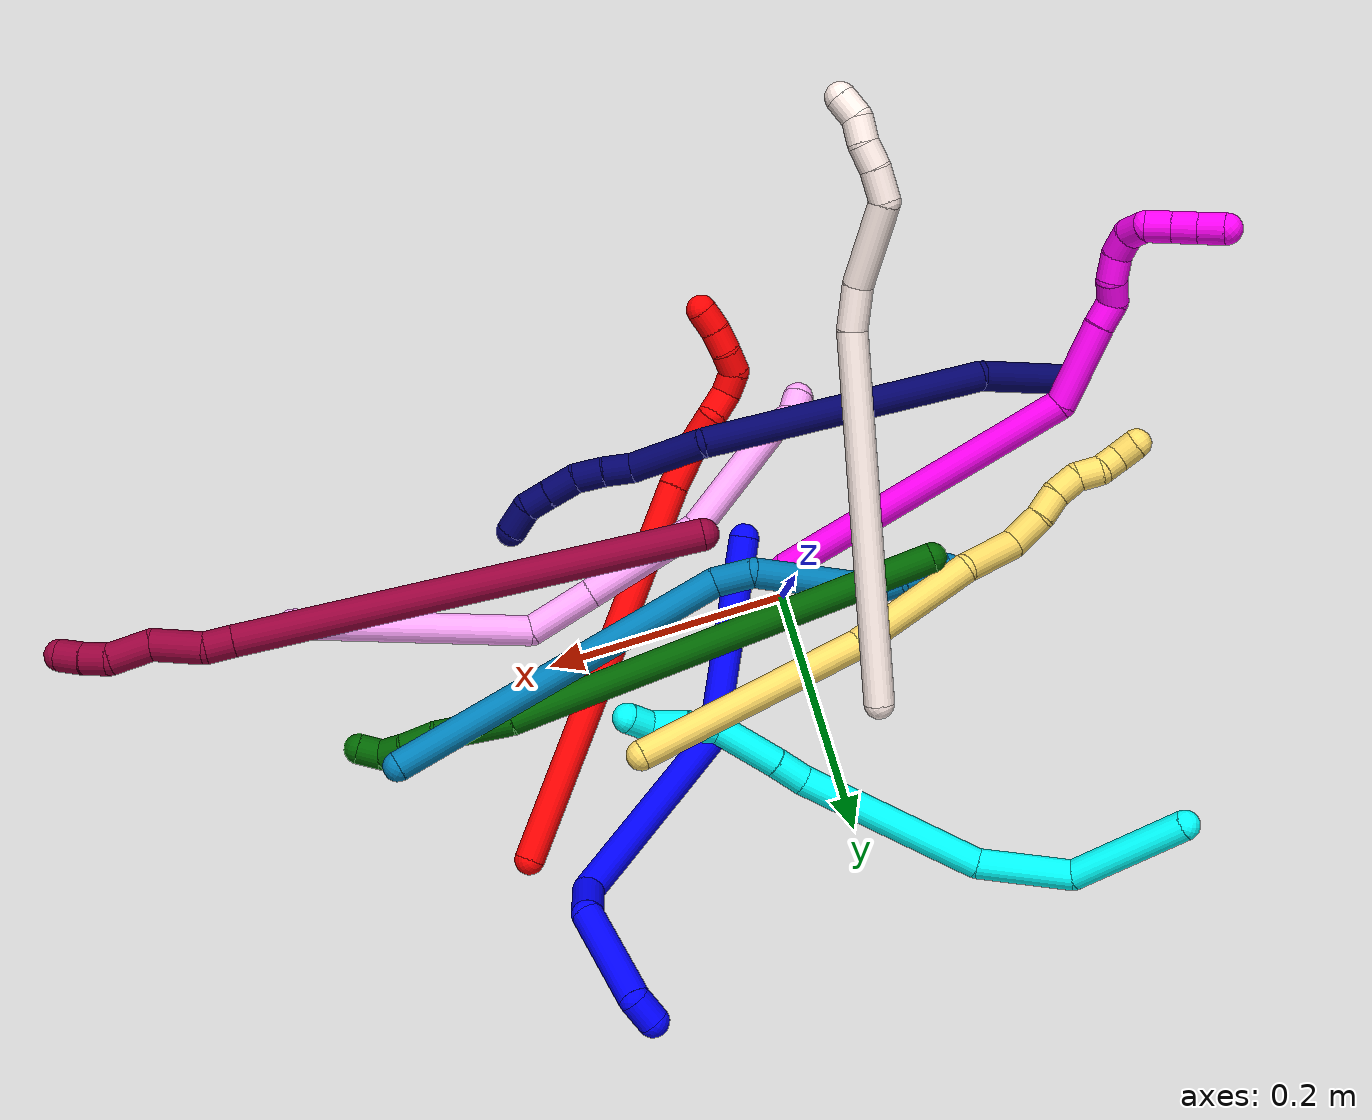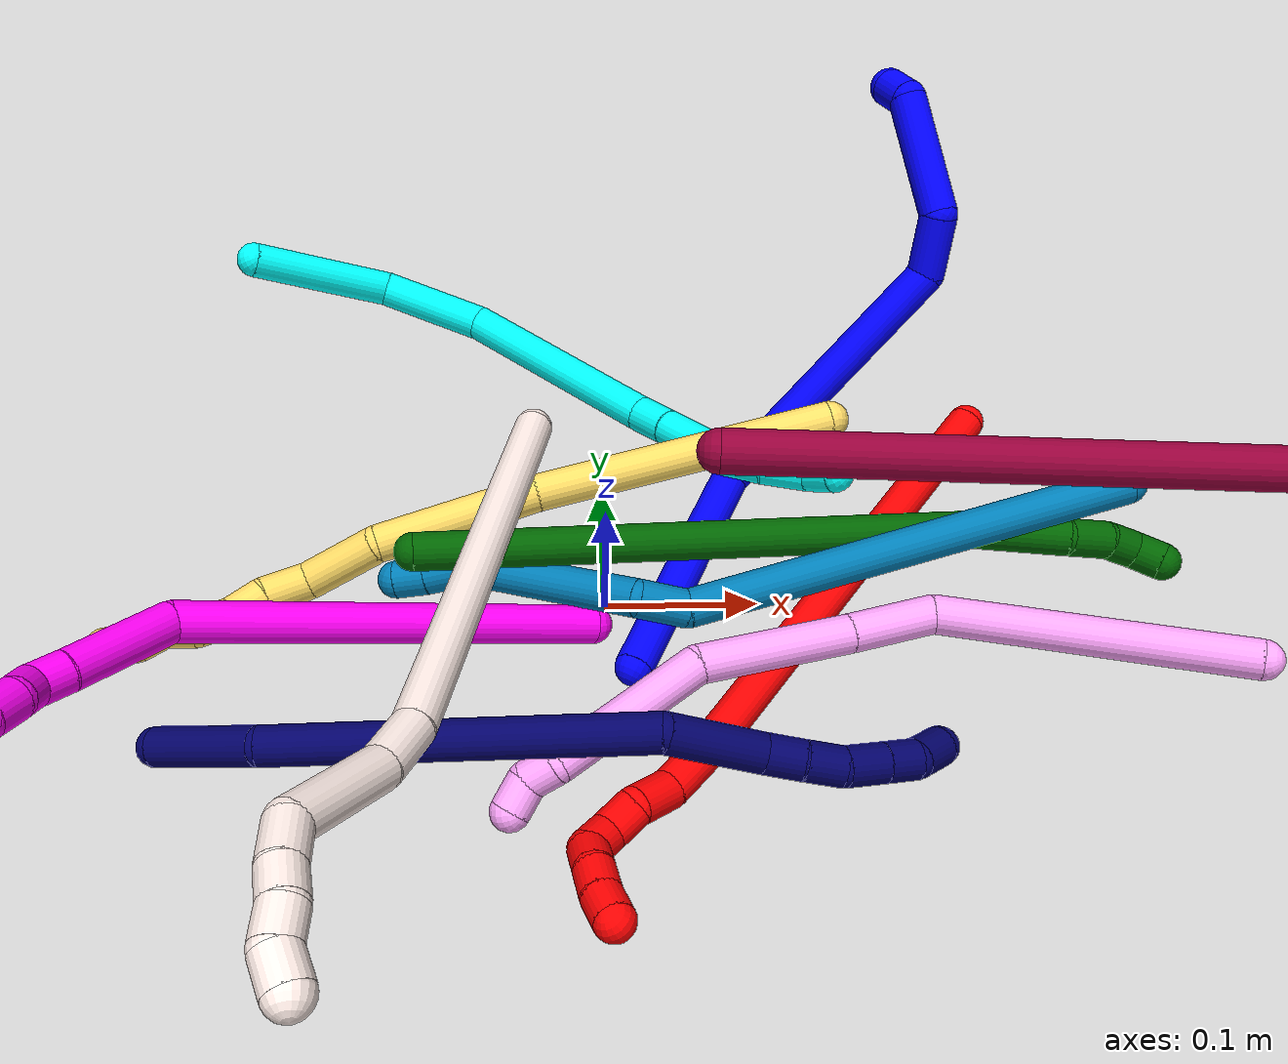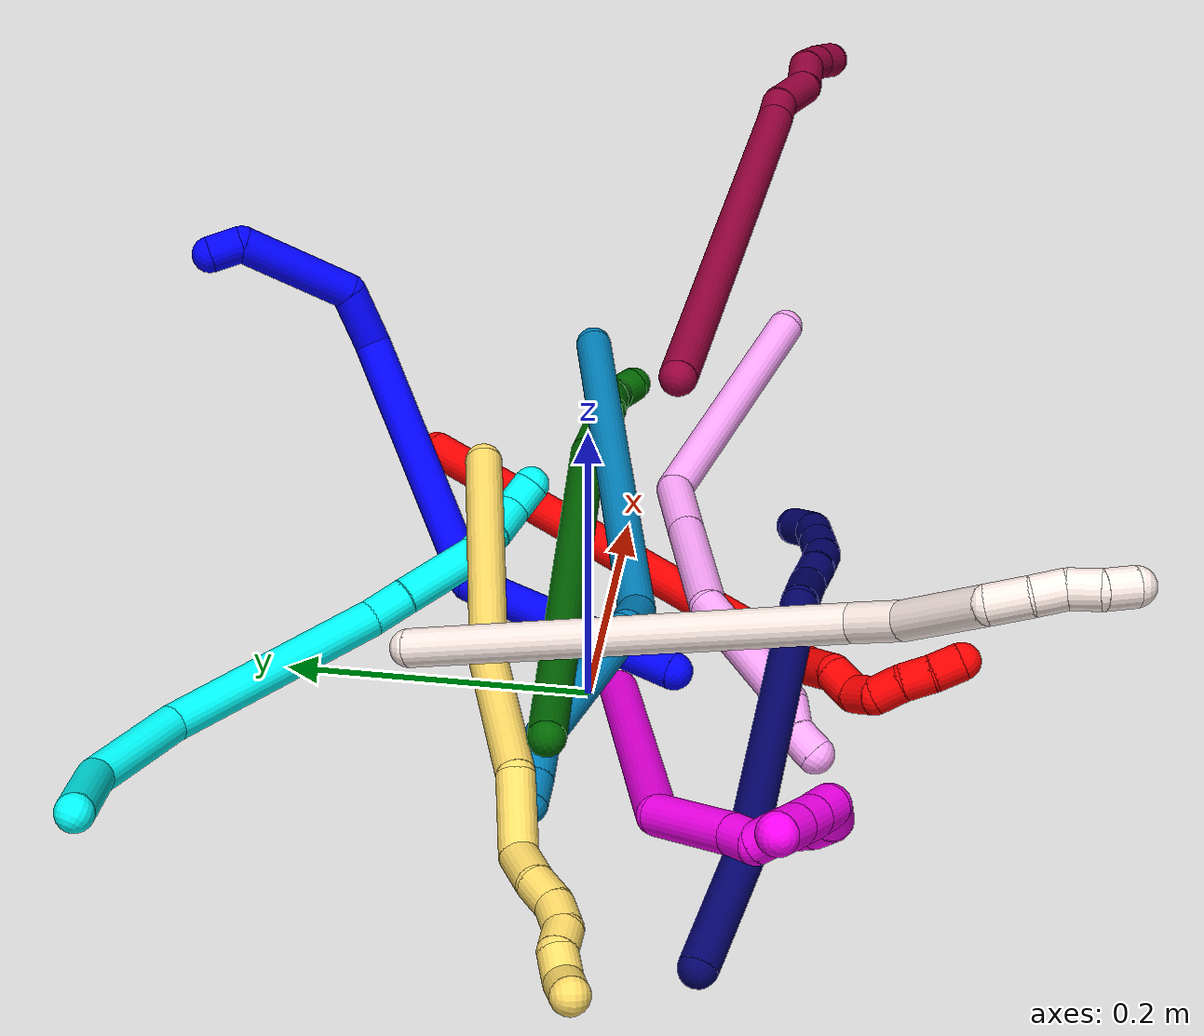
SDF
<sdf version="1.7">
 <world name="default">
  <plugin name="TubeGeneratorPlugin" filename="libtube_generator_plugin.so"/>
  <model name="photoneo_s_sensor">
   <static>1</static>
   <pose>0 0 2 1.57079 1.57079 3.14159</pose>
   <link name="link">
    <inertial><mass>0.1</mass></inertial>
    <sensor name="sensor" type="depth">
     <update_rate>30</update_rate>
     <camera>
      <horizontal_fov>1.22</horizontal_fov>
      <image><width>1920</width><height>1200</height><format>B8G8R8</format></image>
      <clip><near>0.1</near><far>4</far></clip>
      <depth_camera><output>points</output></depth_camera>
     </camera>
     <plugin name="camera_plugin" filename="libgazebo_ros_depth_camera.so">
      <baseline>0.2</baseline>
      <alwaysOn>1</alwaysOn>
      <updateRate>0.0</updateRate>
      <cameraName>camera_ir</cameraName>
      <imageTopicName>/camera/color/image_raw</imageTopicName>
      <cameraInfoTopicName>/camera/color/camera_info</cameraInfoTopicName>
      <depthImageTopicName>/camera/depth/image_raw</depthImageTopicName>
      <depthImageCameraInfoTopicName>/camera/depth/camera_info</depthImageCameraInfoTopicName>
      <pointCloudTopicName>/camera/depth/points</pointCloudTopicName>
      <frameName>fr_optical</frameName>
      <pointCloudCutoff>0.1</pointCloudCutoff>
      <pointCloudCutoffMax>2.0</pointCloudCutoffMax>
      <distortionK1>0</distortionK1>
      <distortionK2>0</distortionK2>
      <distortionK3>0</distortionK3>
      <distortionT1>0</distortionT1>
      <distortionT2>0</distortionT2>
      <CxPrime>0</CxPrime>
      <Cx>0</Cx>
      <Cy>0</Cy>
      <focalLength>0</focalLength>
      <hackBaseline>0</hackBaseline>
     </plugin>
    </sensor>
   </link>
  </model>
  <gravity>0 0 -9.8</gravity>
  <magnetic_field>6e-06 2.3e-05 -4.2e-05</magnetic_field>
  <atmosphere type="adiabatic"/>
  <physics name="default_physics" default="0" type="ode">
   <max_step_size>0.003</max_step_size>
   <real_time_factor>1</real_time_factor>
   <real_time_update_rate>1000</real_time_update_rate>
   <max_contacts>10000</max_contacts>
   <ode>
    <solver>
     <type>quick</type>
     <iters>100</iters>
     <sor>1.3</sor>
     <use_dynamic_moi_rescaling>0</use_dynamic_moi_rescaling>
    </solver>
    <constraints>
     <contact_max_correcting_vel>0</contact_max_correcting_vel>
     <contact_surface_layer>0.001</contact_surface_layer>
     <cfm>0</cfm>
     <erp>0.2</erp>
    </constraints>
   </ode>
  </physics>
  <scene><ambient>0.4 0.4 0.4 1</ambient><background>0.7 0.7 0.7 1</background><shadows>0</shadows></scene>
  <audio><device>default</device></audio>
  <spherical_coordinates>
   <surface_model>EARTH_WGS84</surface_model>
   <latitude_deg>0</latitude_deg>
   <longitude_deg>0</longitude_deg>
   <elevation>0</elevation>
   <heading_deg>0</heading_deg>
  </spherical_coordinates>
  <model name="bin">
   <static>1</static>
   <link name="bottom">
    <collision name="collision-bottom">
     <pose>0 0 -0.01 0 -0 0</pose>
     <geometry><box><size>0.8 0.6 0.02</size></box></geometry>
     <surface>
      <friction><ode><mu>100</mu><mu2>100</mu2></ode></friction>
      <contact><collide_bitmask>65535</collide_bitmask></contact>
     </surface>
    </collision>
   </link>
   <link name="west_wall">
    <collision name="collision-west_wall">
     <pose>-0.41 0 0.1 0 -0 0</pose>
     <geometry><box><size>0.02 0.6 0.2</size></box></geometry>
     <surface>
      <friction><ode><mu>100</mu><mu2>100</mu2></ode></friction>
      <contact><collide_bitmask>65535</collide_bitmask></contact>
     </surface>
    </collision>
   </link>
   <link name="east_wall">
    <collision name="collision-east_wall">
     <pose>0.41 0 0.1 0 -0 0</pose>
     <geometry><box><size>0.02 0.6 0.2</size></box></geometry>
     <surface>
      <friction><ode><mu>100</mu><mu2>100</mu2></ode></friction>
      <contact><collide_bitmask>65535</collide_bitmask></contact>
     </surface>
    </collision>
   </link>
   <link name="south_wall">
    <collision name="collision-south_wall">
     <pose>0 -0.31 0.1 0 -0 0</pose>
     <geometry><box><size>0.8 0.02 0.2</size></box></geometry>
     <surface>
      <friction><ode><mu>100</mu><mu2>100</mu2></ode></friction>
      <contact><collide_bitmask>65535</collide_bitmask></contact>
     </surface>
    </collision>
   </link>
   <link name="north_wall">
    <collision name="collision-north_wall">
     <pose>0 0.31 0.1 0 -0 0</pose>
     <geometry><box><size>0.8 0.02 0.2</size></box></geometry>
     <surface>
      <friction><ode><mu>100</mu><mu2>100</mu2></ode></friction>
      <contact><collide_bitmask>65535</collide_bitmask></contact>
     </surface>
    </collision>
   </link>
  </model>
  <model name="1">
   <static>0</static>
   <link name="1">
    <collision name="collision-cylinder-e_1_1_4">
     <pose>-0.024571 0.014627 0.077378 -0.186833 -0.302445 0.028552</pose>
     <geometry><cylinder><radius>0.0125</radius><length>0.164985</length></cylinder></geometry>
     <surface>
      <friction><ode><mu>1.16</mu><mu2>1.16</mu2><slip1>0</slip1><slip2>0</slip2></ode></friction>
      <contact><ode><kp>1e+06</kp><kd>1</kd><max_vel>0</max_vel><min_depth>0.001</min_depth></ode></contact>
     </surface>
    </collision>
    <visual name="visual-cylinder-e_1_1_4">
     <pose>-0.024571 0.014627 0.077378 -0.186833 -0.302445 0.028552</pose>
     <geometry><cylinder><radius>0.0125</radius><length>0.164985</length></cylinder></geometry>
     <material><ambient>0 0 1 1</ambient></material>
    </visual>
    <collision name="collision-cylinder-e_2_4_5">
     <pose>-0.010215 0.04276 0.239758 -0.157559 0.424744 -0.034041</pose>
     <geometry><cylinder><radius>0.0125</radius><length>0.188925</length></cylinder></geometry>
     <surface>
      <friction><ode><mu>1.16</mu><mu2>1.16</mu2><slip1>0</slip1><slip2>0</slip2></ode></friction>
      <contact><ode><kp>1e+06</kp><kd>1</kd><max_vel>0</max_vel><min_depth>0.001</min_depth></ode></contact>
     </surface>
    </collision>
    <visual name="visual-cylinder-e_2_4_5">
     <pose>-0.010215 0.04276 0.239758 -0.157559 0.424744 -0.034041</pose>
     <geometry><cylinder><radius>0.0125</radius><length>0.188925</length></cylinder></geometry>
     <material><ambient>0 0 1 1</ambient></material>
    </visual>
    <collision name="collision-cylinder-e_3_5_6">
     <pose>0.038167 0.045637 0.339754 0.616637 0.475181 0.153942</pose>
     <geometry><cylinder><radius>0.0125</radius><length>0.041334</length></cylinder></geometry>
     <surface>
      <friction><ode><mu>1.16</mu><mu2>1.16</mu2><slip1>0</slip1><slip2>0</slip2></ode></friction>
      <contact><ode><kp>1e+06</kp><kd>1</kd><max_vel>0</max_vel><min_depth>0.001</min_depth></ode></contact>
     </surface>
    </collision>
    <visual name="visual-cylinder-e_3_5_6">
     <pose>0.038167 0.045637 0.339754 0.616637 0.475181 0.153942</pose>
     <geometry><cylinder><radius>0.0125</radius><length>0.041334</length></cylinder></geometry>
     <material><ambient>0 0 1 1</ambient></material>
    </visual>
    <collision name="collision-cylinder-e_4_6_7">
     <pose>0.038801 0.010636 0.386656 0.652299 -0.21625 -0.073395</pose>
     <geometry><cylinder><radius>0.0125</radius><length>0.082222</length></cylinder></geometry>
     <surface>
      <friction><ode><mu>1.16</mu><mu2>1.16</mu2><slip1>0</slip1><slip2>0</slip2></ode></friction>
      <contact><ode><kp>1e+06</kp><kd>1</kd><max_vel>0</max_vel><min_depth>0.001</min_depth></ode></contact>
     </surface>
    </collision>
    <visual name="visual-cylinder-e_4_6_7">
     <pose>0.038801 0.010636 0.386656 0.652299 -0.21625 -0.073395</pose>
     <geometry><cylinder><radius>0.0125</radius><length>0.082222</length></cylinder></geometry>
     <material><ambient>0 0 1 1</ambient></material>
    </visual>
    <collision name="collision-cylinder-e_5_7_2">
     <pose>0.020613 -0.017142 0.423822 0.5748 -0.981467 -0.313291</pose>
     <geometry><cylinder><radius>0.0125</radius><length>0.022535</length></cylinder></geometry>
     <surface>
      <friction><ode><mu>1.16</mu><mu2>1.16</mu2><slip1>0</slip1><slip2>0</slip2></ode></friction>
      <contact><ode><kp>1e+06</kp><kd>1</kd><max_vel>0</max_vel><min_depth>0.001</min_depth></ode></contact>
     </surface>
    </collision>
    <visual name="visual-cylinder-e_5_7_2">
     <pose>0.020613 -0.017142 0.423822 0.5748 -0.981467 -0.313291</pose>
     <geometry><cylinder><radius>0.0125</radius><length>0.022535</length></cylinder></geometry>
     <material><ambient>0 0 1 1</ambient></material>
    </visual>
    <collision name="collision-sphere-2">
     <pose>0.011247 -0.020547 0.429078 0 -0 0</pose>
     <geometry><sphere><radius>0.0125</radius></sphere></geometry>
     <surface>
      <friction><ode><mu>1.16</mu><mu2>1.16</mu2><slip1>0</slip1><slip2>0</slip2></ode></friction>
      <contact><ode><kp>1e+06</kp><kd>1</kd><max_vel>0</max_vel><min_depth>0.001</min_depth></ode></contact>
     </surface>
    </collision>
    <visual name="visual-sphere-2">
     <pose>0.011247 -0.020547 0.429078 0 -0 0</pose>
     <geometry><sphere><radius>0.0125</radius></sphere></geometry>
     <material><ambient>0 0 1 1</ambient></material>
    </visual>
    <collision name="collision-sphere-7">
     <pose>0.02998 -0.013738 0.418565 0 -0 0</pose>
     <geometry><sphere><radius>0.0125</radius></sphere></geometry>
     <surface>
      <friction><ode><mu>1.16</mu><mu2>1.16</mu2><slip1>0</slip1><slip2>0</slip2></ode></friction>
      <contact><ode><kp>1e+06</kp><kd>1</kd><max_vel>0</max_vel><min_depth>0.001</min_depth></ode></contact>
     </surface>
    </collision>
    <visual name="visual-sphere-7">
     <pose>0.02998 -0.013738 0.418565 0 -0 0</pose>
     <geometry><sphere><radius>0.0125</radius></sphere></geometry>
     <material><ambient>0 0 1 1</ambient></material>
    </visual>
    <collision name="collision-sphere-6">
     <pose>0.047622 0.03501 0.354746 0 -0 0</pose>
     <geometry><sphere><radius>0.0125</radius></sphere></geometry>
     <surface>
      <friction><ode><mu>1.16</mu><mu2>1.16</mu2><slip1>0</slip1><slip2>0</slip2></ode></friction>
      <contact><ode><kp>1e+06</kp><kd>1</kd><max_vel>0</max_vel><min_depth>0.001</min_depth></ode></contact>
     </surface>
    </collision>
    <visual name="visual-sphere-6">
     <pose>0.047622 0.03501 0.354746 0 -0 0</pose>
     <geometry><sphere><radius>0.0125</radius></sphere></geometry>
     <material><ambient>0 0 1 1</ambient></material>
    </visual>
    <collision name="collision-sphere-5">
     <pose>0.028712 0.056265 0.324761 0 -0 0</pose>
     <geometry><sphere><radius>0.0125</radius></sphere></geometry>
     <surface>
      <friction><ode><mu>1.16</mu><mu2>1.16</mu2><slip1>0</slip1><slip2>0</slip2></ode></friction>
      <contact><ode><kp>1e+06</kp><kd>1</kd><max_vel>0</max_vel><min_depth>0.001</min_depth></ode></contact>
     </surface>
    </collision>
    <visual name="visual-sphere-5">
     <pose>0.028712 0.056265 0.324761 0 -0 0</pose>
     <geometry><sphere><radius>0.0125</radius></sphere></geometry>
     <material><ambient>0 0 1 1</ambient></material>
    </visual>
    <collision name="collision-sphere-1">
     <geometry><sphere><radius>0.0125</radius></sphere></geometry>
     <surface>
      <friction><ode><mu>1.16</mu><mu2>1.16</mu2><slip1>0</slip1><slip2>0</slip2></ode></friction>
      <contact><ode><kp>1e+06</kp><kd>1</kd><max_vel>0</max_vel><min_depth>0.001</min_depth></ode></contact>
     </surface>
    </collision>
    <visual name="visual-sphere-1">
     <geometry><sphere><radius>0.0125</radius></sphere></geometry>
     <material><ambient>0 0 1 1</ambient></material>
    </visual>
    <collision name="collision-sphere-4">
     <pose>-0.049142 0.029255 0.154756 0 -0 0</pose>
     <geometry><sphere><radius>0.0125</radius></sphere></geometry>
     <surface>
      <friction><ode><mu>1.16</mu><mu2>1.16</mu2><slip1>0</slip1><slip2>0</slip2></ode></friction>
      <contact><ode><kp>1e+06</kp><kd>1</kd><max_vel>0</max_vel><min_depth>0.001</min_depth></ode></contact>
     </surface>
    </collision>
    <visual name="visual-sphere-4">
     <pose>-0.049142 0.029255 0.154756 0 -0 0</pose>
     <geometry><sphere><radius>0.0125</radius></sphere></geometry>
     <material><ambient>0 0 1 1</ambient></material>
    </visual>
    <inertial>
     <pose>-0.001502 0.025732 0.226896 0 -0 0</pose>
     <mass>0.5</mass>
     <inertia>
      <ixx>0.000928</ixx>
      <ixy>0</ixy>
      <ixz>0</ixz>
      <iyy>0.000974</iyy>
      <iyz>0</iyz>
      <izz>-0.000194</izz>
     </inertia>
    </inertial>
   </link>
   <pose>0.016674 -0.054532 0.011492 -1.00902 -0.779038 -0.927954</pose>
  </model>
  <model name="2">
   <static>0</static>
   <link name="2">
    <collision name="collision-cylinder-e_1_1_4">
     <pose>-0.081338 -0.140689 0.024939 1.39536 -0.517515 -0.43672</pose>
     <geometry><cylinder><radius>0.0125</radius><length>0.328824</length></cylinder></geometry>
     <surface>
      <friction><ode><mu>1.16</mu><mu2>1.16</mu2><slip1>0</slip1><slip2>0</slip2></ode></friction>
      <contact><ode><kp>1e+06</kp><kd>1</kd><max_vel>0</max_vel><min_depth>0.001</min_depth></ode></contact>
     </surface>
    </collision>
    <visual name="visual-cylinder-e_1_1_4">
     <pose>-0.081338 -0.140689 0.024939 1.39536 -0.517515 -0.43672</pose>
     <geometry><cylinder><radius>0.0125</radius><length>0.328824</length></cylinder></geometry>
     <material><ambient>1 0 0 1</ambient></material>
    </visual>
    <collision name="collision-cylinder-e_2_4_5">
     <pose>-0.173275 -0.297369 0.053878 1.32564 -0.571413 -0.450817</pose>
     <geometry><cylinder><radius>0.0125</radius><length>0.039192</length></cylinder></geometry>
     <surface>
      <friction><ode><mu>1.16</mu><mu2>1.16</mu2><slip1>0</slip1><slip2>0</slip2></ode></friction>
      <contact><ode><kp>1e+06</kp><kd>1</kd><max_vel>0</max_vel><min_depth>0.001</min_depth></ode></contact>
     </surface>
    </collision>
    <visual name="visual-cylinder-e_2_4_5">
     <pose>-0.173275 -0.297369 0.053878 1.32564 -0.571413 -0.450817</pose>
     <geometry><cylinder><radius>0.0125</radius><length>0.039192</length></cylinder></geometry>
     <material><ambient>1 0 0 1</ambient></material>
    </visual>
    <collision name="collision-cylinder-e_3_5_6">
     <pose>-0.189959 -0.323875 0.066426 0.888284 -0.422154 -0.203217</pose>
     <geometry><cylinder><radius>0.0125</radius><length>0.029712</length></cylinder></geometry>
     <surface>
      <friction><ode><mu>1.16</mu><mu2>1.16</mu2><slip1>0</slip1><slip2>0</slip2></ode></friction>
      <contact><ode><kp>1e+06</kp><kd>1</kd><max_vel>0</max_vel><min_depth>0.001</min_depth></ode></contact>
     </surface>
    </collision>
    <visual name="visual-cylinder-e_3_5_6">
     <pose>-0.189959 -0.323875 0.066426 0.888284 -0.422154 -0.203217</pose>
     <geometry><cylinder><radius>0.0125</radius><length>0.029712</length></cylinder></geometry>
     <material><ambient>1 0 0 1</ambient></material>
    </visual>
    <collision name="collision-cylinder-e_4_6_7">
     <pose>-0.203669 -0.34236 0.075994 1.44355 -0.759115 -0.675341</pose>
     <geometry><cylinder><radius>0.0125</radius><length>0.022149</length></cylinder></geometry>
     <surface>
      <friction><ode><mu>1.16</mu><mu2>1.16</mu2><slip1>0</slip1><slip2>0</slip2></ode></friction>
      <contact><ode><kp>1e+06</kp><kd>1</kd><max_vel>0</max_vel><min_depth>0.001</min_depth></ode></contact>
     </surface>
    </collision>
    <visual name="visual-cylinder-e_4_6_7">
     <pose>-0.203669 -0.34236 0.075994 1.44355 -0.759115 -0.675341</pose>
     <geometry><cylinder><radius>0.0125</radius><length>0.022149</length></cylinder></geometry>
     <material><ambient>1 0 0 1</ambient></material>
    </visual>
    <collision name="collision-cylinder-e_5_7_8">
     <pose>-0.214045 -0.358622 0.081984 1.03083 -0.27749 -0.157883</pose>
     <geometry><cylinder><radius>0.0125</radius><length>0.020105</length></cylinder></geometry>
     <surface>
      <friction><ode><mu>1.16</mu><mu2>1.16</mu2><slip1>0</slip1><slip2>0</slip2></ode></friction>
      <contact><ode><kp>1e+06</kp><kd>1</kd><max_vel>0</max_vel><min_depth>0.001</min_depth></ode></contact>
     </surface>
    </collision>
    <visual name="visual-cylinder-e_5_7_8">
     <pose>-0.214045 -0.358622 0.081984 1.03083 -0.27749 -0.157883</pose>
     <geometry><cylinder><radius>0.0125</radius><length>0.020105</length></cylinder></geometry>
     <material><ambient>1 0 0 1</ambient></material>
    </visual>
    <collision name="collision-cylinder-e_6_8_9">
     <pose>-0.212675 -0.375698 0.089386 1.30072 0.424891 0.325299</pose>
     <geometry><cylinder><radius>0.0125</radius><length>0.020006</length></cylinder></geometry>
     <surface>
      <friction><ode><mu>1.16</mu><mu2>1.16</mu2><slip1>0</slip1><slip2>0</slip2></ode></friction>
      <contact><ode><kp>1e+06</kp><kd>1</kd><max_vel>0</max_vel><min_depth>0.001</min_depth></ode></contact>
     </surface>
    </collision>
    <visual name="visual-cylinder-e_6_8_9">
     <pose>-0.212675 -0.375698 0.089386 1.30072 0.424891 0.325299</pose>
     <geometry><cylinder><radius>0.0125</radius><length>0.020006</length></cylinder></geometry>
     <material><ambient>1 0 0 1</ambient></material>
    </visual>
    <collision name="collision-cylinder-e_7_9_10">
     <pose>-0.204902 -0.393775 0.092417 1.50639 0.373503 0.350679</pose>
     <geometry><cylinder><radius>0.0125</radius><length>0.020007</length></cylinder></geometry>
     <surface>
      <friction><ode><mu>1.16</mu><mu2>1.16</mu2><slip1>0</slip1><slip2>0</slip2></ode></friction>
      <contact><ode><kp>1e+06</kp><kd>1</kd><max_vel>0</max_vel><min_depth>0.001</min_depth></ode></contact>
     </surface>
    </collision>
    <visual name="visual-cylinder-e_7_9_10">
     <pose>-0.204902 -0.393775 0.092417 1.50639 0.373503 0.350679</pose>
     <geometry><cylinder><radius>0.0125</radius><length>0.020007</length></cylinder></geometry>
     <material><ambient>1 0 0 1</ambient></material>
    </visual>
    <collision name="collision-cylinder-e_8_10_2">
     <pose>-0.196329 -0.411776 0.093109 1.56012 0.514537 0.509309</pose>
     <geometry><cylinder><radius>0.0125</radius><length>0.020004</length></cylinder></geometry>
     <surface>
      <friction><ode><mu>1.16</mu><mu2>1.16</mu2><slip1>0</slip1><slip2>0</slip2></ode></friction>
      <contact><ode><kp>1e+06</kp><kd>1</kd><max_vel>0</max_vel><min_depth>0.001</min_depth></ode></contact>
     </surface>
    </collision>
    <visual name="visual-cylinder-e_8_10_2">
     <pose>-0.196329 -0.411776 0.093109 1.56012 0.514537 0.509309</pose>
     <geometry><cylinder><radius>0.0125</radius><length>0.020004</length></cylinder></geometry>
     <material><ambient>1 0 0 1</ambient></material>
    </visual>
    <collision name="collision-sphere-2">
     <pose>-0.191407 -0.420483 0.093202 0 -0 0</pose>
     <geometry><sphere><radius>0.0125</radius></sphere></geometry>
     <surface>
      <friction><ode><mu>1.16</mu><mu2>1.16</mu2><slip1>0</slip1><slip2>0</slip2></ode></friction>
      <contact><ode><kp>1e+06</kp><kd>1</kd><max_vel>0</max_vel><min_depth>0.001</min_depth></ode></contact>
     </surface>
    </collision>
    <visual name="visual-sphere-2">
     <pose>-0.191407 -0.420483 0.093202 0 -0 0</pose>
     <geometry><sphere><radius>0.0125</radius></sphere></geometry>
     <material><ambient>1 0 0 1</ambient></material>
    </visual>
    <collision name="collision-sphere-10">
     <pose>-0.201252 -0.40307 0.093016 0 -0 0</pose>
     <geometry><sphere><radius>0.0125</radius></sphere></geometry>
     <surface>
      <friction><ode><mu>1.16</mu><mu2>1.16</mu2><slip1>0</slip1><slip2>0</slip2></ode></friction>
      <contact><ode><kp>1e+06</kp><kd>1</kd><max_vel>0</max_vel><min_depth>0.001</min_depth></ode></contact>
     </surface>
    </collision>
    <visual name="visual-sphere-10">
     <pose>-0.201252 -0.40307 0.093016 0 -0 0</pose>
     <geometry><sphere><radius>0.0125</radius></sphere></geometry>
     <material><ambient>1 0 0 1</ambient></material>
    </visual>
    <collision name="collision-sphere-9">
     <pose>-0.208552 -0.384481 0.091817 0 -0 0</pose>
     <geometry><sphere><radius>0.0125</radius></sphere></geometry>
     <surface>
      <friction><ode><mu>1.16</mu><mu2>1.16</mu2><slip1>0</slip1><slip2>0</slip2></ode></friction>
      <contact><ode><kp>1e+06</kp><kd>1</kd><max_vel>0</max_vel><min_depth>0.001</min_depth></ode></contact>
     </surface>
    </collision>
    <visual name="visual-sphere-9">
     <pose>-0.208552 -0.384481 0.091817 0 -0 0</pose>
     <geometry><sphere><radius>0.0125</radius></sphere></geometry>
     <material><ambient>1 0 0 1</ambient></material>
    </visual>
    <collision name="collision-sphere-4">
     <pose>-0.162677 -0.281379 0.049878 0 -0 0</pose>
     <geometry><sphere><radius>0.0125</radius></sphere></geometry>
     <surface>
      <friction><ode><mu>1.16</mu><mu2>1.16</mu2><slip1>0</slip1><slip2>0</slip2></ode></friction>
      <contact><ode><kp>1e+06</kp><kd>1</kd><max_vel>0</max_vel><min_depth>0.001</min_depth></ode></contact>
     </surface>
    </collision>
    <visual name="visual-sphere-4">
     <pose>-0.162677 -0.281379 0.049878 0 -0 0</pose>
     <geometry><sphere><radius>0.0125</radius></sphere></geometry>
     <material><ambient>1 0 0 1</ambient></material>
    </visual>
    <collision name="collision-sphere-1">
     <geometry><sphere><radius>0.0125</radius></sphere></geometry>
     <surface>
      <friction><ode><mu>1.16</mu><mu2>1.16</mu2><slip1>0</slip1><slip2>0</slip2></ode></friction>
      <contact><ode><kp>1e+06</kp><kd>1</kd><max_vel>0</max_vel><min_depth>0.001</min_depth></ode></contact>
     </surface>
    </collision>
    <visual name="visual-sphere-1">
     <geometry><sphere><radius>0.0125</radius></sphere></geometry>
     <material><ambient>1 0 0 1</ambient></material>
    </visual>
    <collision name="collision-sphere-8">
     <pose>-0.216799 -0.366914 0.086954 0 -0 0</pose>
     <geometry><sphere><radius>0.0125</radius></sphere></geometry>
     <surface>
      <friction><ode><mu>1.16</mu><mu2>1.16</mu2><slip1>0</slip1><slip2>0</slip2></ode></friction>
      <contact><ode><kp>1e+06</kp><kd>1</kd><max_vel>0</max_vel><min_depth>0.001</min_depth></ode></contact>
     </surface>
    </collision>
    <visual name="visual-sphere-8">
     <pose>-0.216799 -0.366914 0.086954 0 -0 0</pose>
     <geometry><sphere><radius>0.0125</radius></sphere></geometry>
     <material><ambient>1 0 0 1</ambient></material>
    </visual>
    <collision name="collision-sphere-5">
     <pose>-0.183873 -0.313359 0.057879 0 -0 0</pose>
     <geometry><sphere><radius>0.0125</radius></sphere></geometry>
     <surface>
      <friction><ode><mu>1.16</mu><mu2>1.16</mu2><slip1>0</slip1><slip2>0</slip2></ode></friction>
      <contact><ode><kp>1e+06</kp><kd>1</kd><max_vel>0</max_vel><min_depth>0.001</min_depth></ode></contact>
     </surface>
    </collision>
    <visual name="visual-sphere-5">
     <pose>-0.183873 -0.313359 0.057879 0 -0 0</pose>
     <geometry><sphere><radius>0.0125</radius></sphere></geometry>
     <material><ambient>1 0 0 1</ambient></material>
    </visual>
    <collision name="collision-sphere-6">
     <pose>-0.196046 -0.334391 0.074974 0 -0 0</pose>
     <geometry><sphere><radius>0.0125</radius></sphere></geometry>
     <surface>
      <friction><ode><mu>1.16</mu><mu2>1.16</mu2><slip1>0</slip1><slip2>0</slip2></ode></friction>
      <contact><ode><kp>1e+06</kp><kd>1</kd><max_vel>0</max_vel><min_depth>0.001</min_depth></ode></contact>
     </surface>
    </collision>
    <visual name="visual-sphere-6">
     <pose>-0.196046 -0.334391 0.074974 0 -0 0</pose>
     <geometry><sphere><radius>0.0125</radius></sphere></geometry>
     <material><ambient>1 0 0 1</ambient></material>
    </visual>
    <collision name="collision-sphere-7">
     <pose>-0.211291 -0.350329 0.077013 0 -0 0</pose>
     <geometry><sphere><radius>0.0125</radius></sphere></geometry>
     <surface>
      <friction><ode><mu>1.16</mu><mu2>1.16</mu2><slip1>0</slip1><slip2>0</slip2></ode></friction>
      <contact><ode><kp>1e+06</kp><kd>1</kd><max_vel>0</max_vel><min_depth>0.001</min_depth></ode></contact>
     </surface>
    </collision>
    <visual name="visual-sphere-7">
     <pose>-0.211291 -0.350329 0.077013 0 -0 0</pose>
     <geometry><sphere><radius>0.0125</radius></sphere></geometry>
     <material><ambient>1 0 0 1</ambient></material>
    </visual>
    <inertial>
     <pose>-0.120554 -0.211929 0.042234 0 -0 0</pose>
     <mass>0.5</mass>
     <inertia>
      <ixx>0.001246</ixx>
      <ixy>0</ixy>
      <ixz>0</ixz>
      <iyy>-3.7e-05</iyy>
      <iyz>0</iyz>
      <izz>0.004045</izz>
     </inertia>
    </inertial>
   </link>
   <pose>0.261971 0.146852 0.011496 -0.128845 -0.484479 -0.067757</pose>
  </model>
  <model name="3">
   <static>0</static>
   <link name="3">
    <collision name="collision-cylinder-e_1_1_4">
     <pose>-0.001968 -0.047898 -0.018093 1.93197 -0.038408 -0.055558</pose>
     <geometry><cylinder><radius>0.0125</radius><length>0.102478</length></cylinder></geometry>
     <surface>
      <friction><ode><mu>1.16</mu><mu2>1.16</mu2><slip1>0</slip1><slip2>0</slip2></ode></friction>
      <contact><ode><kp>1e+06</kp><kd>1</kd><max_vel>0</max_vel><min_depth>0.001</min_depth></ode></contact>
     </surface>
    </collision>
    <visual name="visual-cylinder-e_1_1_4">
     <pose>-0.001968 -0.047898 -0.018093 1.93197 -0.038408 -0.055558</pose>
     <geometry><cylinder><radius>0.0125</radius><length>0.102478</length></cylinder></geometry>
     <material><ambient>0.003922 1 0.996078 1</ambient></material>
    </visual>
    <collision name="collision-cylinder-e_2_4_5">
     <pose>0.00968 -0.119018 -0.064852 2.46072 0.353561 0.934202</pose>
     <geometry><cylinder><radius>0.0125</radius><length>0.078647</length></cylinder></geometry>
     <surface>
      <friction><ode><mu>1.16</mu><mu2>1.16</mu2><slip1>0</slip1><slip2>0</slip2></ode></friction>
      <contact><ode><kp>1e+06</kp><kd>1</kd><max_vel>0</max_vel><min_depth>0.001</min_depth></ode></contact>
     </surface>
    </collision>
    <visual name="visual-cylinder-e_2_4_5">
     <pose>0.00968 -0.119018 -0.064852 2.46072 0.353561 0.934202</pose>
     <geometry><cylinder><radius>0.0125</radius><length>0.078647</length></cylinder></geometry>
     <material><ambient>0.003922 1 0.996078 1</ambient></material>
    </visual>
    <collision name="collision-cylinder-e_3_5_6">
     <pose>0.066566 -0.165205 -0.155568 2.78713 0.579172 2.05911</pose>
     <geometry><cylinder><radius>0.0125</radius><length>0.158114</length></cylinder></geometry>
     <surface>
      <friction><ode><mu>1.16</mu><mu2>1.16</mu2><slip1>0</slip1><slip2>0</slip2></ode></friction>
      <contact><ode><kp>1e+06</kp><kd>1</kd><max_vel>0</max_vel><min_depth>0.001</min_depth></ode></contact>
     </surface>
    </collision>
    <visual name="visual-cylinder-e_3_5_6">
     <pose>0.066566 -0.165205 -0.155568 2.78713 0.579172 2.05911</pose>
     <geometry><cylinder><radius>0.0125</radius><length>0.158114</length></cylinder></geometry>
     <material><ambient>0.003922 1 0.996078 1</ambient></material>
    </visual>
    <collision name="collision-cylinder-e_4_6_7">
     <pose>0.117251 -0.189164 -0.22936 3.05711 0.56163 2.85061</pose>
     <geometry><cylinder><radius>0.0125</radius><length>0.027843</length></cylinder></geometry>
     <surface>
      <friction><ode><mu>1.16</mu><mu2>1.16</mu2><slip1>0</slip1><slip2>0</slip2></ode></friction>
      <contact><ode><kp>1e+06</kp><kd>1</kd><max_vel>0</max_vel><min_depth>0.001</min_depth></ode></contact>
     </surface>
    </collision>
    <visual name="visual-cylinder-e_4_6_7">
     <pose>0.117251 -0.189164 -0.22936 3.05711 0.56163 2.85061</pose>
     <geometry><cylinder><radius>0.0125</radius><length>0.027843</length></cylinder></geometry>
     <material><ambient>0.003922 1 0.996078 1</ambient></material>
    </visual>
    <collision name="collision-cylinder-e_5_7_8">
     <pose>0.139539 -0.193934 -0.264356 2.98063 0.563126 2.59773</pose>
     <geometry><cylinder><radius>0.0125</radius><length>0.055725</length></cylinder></geometry>
     <surface>
      <friction><ode><mu>1.16</mu><mu2>1.16</mu2><slip1>0</slip1><slip2>0</slip2></ode></friction>
      <contact><ode><kp>1e+06</kp><kd>1</kd><max_vel>0</max_vel><min_depth>0.001</min_depth></ode></contact>
     </surface>
    </collision>
    <visual name="visual-cylinder-e_5_7_8">
     <pose>0.139539 -0.193934 -0.264356 2.98063 0.563126 2.59773</pose>
     <geometry><cylinder><radius>0.0125</radius><length>0.055725</length></cylinder></geometry>
     <material><ambient>0.003922 1 0.996078 1</ambient></material>
    </visual>
    <collision name="collision-cylinder-e_6_8_9">
     <pose>0.157606 -0.203747 -0.298143 2.62103 0.257269 0.904261</pose>
     <geometry><cylinder><radius>0.0125</radius><length>0.025105</length></cylinder></geometry>
     <surface>
      <friction><ode><mu>1.16</mu><mu2>1.16</mu2><slip1>0</slip1><slip2>0</slip2></ode></friction>
      <contact><ode><kp>1e+06</kp><kd>1</kd><max_vel>0</max_vel><min_depth>0.001</min_depth></ode></contact>
     </surface>
    </collision>
    <visual name="visual-cylinder-e_6_8_9">
     <pose>0.157606 -0.203747 -0.298143 2.62103 0.257269 0.904261</pose>
     <geometry><cylinder><radius>0.0125</radius><length>0.025105</length></cylinder></geometry>
     <material><ambient>0.003922 1 0.996078 1</ambient></material>
    </visual>
    <collision name="collision-cylinder-e_7_9_10">
     <pose>0.163422 -0.217726 -0.321437 2.585 0.172689 0.588343</pose>
     <geometry><cylinder><radius>0.0125</radius><length>0.030516</length></cylinder></geometry>
     <surface>
      <friction><ode><mu>1.16</mu><mu2>1.16</mu2><slip1>0</slip1><slip2>0</slip2></ode></friction>
      <contact><ode><kp>1e+06</kp><kd>1</kd><max_vel>0</max_vel><min_depth>0.001</min_depth></ode></contact>
     </surface>
    </collision>
    <visual name="visual-cylinder-e_7_9_10">
     <pose>0.163422 -0.217726 -0.321437 2.585 0.172689 0.588343</pose>
     <geometry><cylinder><radius>0.0125</radius><length>0.030516</length></cylinder></geometry>
     <material><ambient>0.003922 1 0.996078 1</ambient></material>
    </visual>
    <collision name="collision-cylinder-e_8_10_2">
     <pose>0.168485 -0.225599 -0.344705 -3.1352 0.228326 -3.08587</pose>
     <geometry><cylinder><radius>0.0125</radius><length>0.021572</length></cylinder></geometry>
     <surface>
      <friction><ode><mu>1.16</mu><mu2>1.16</mu2><slip1>0</slip1><slip2>0</slip2></ode></friction>
      <contact><ode><kp>1e+06</kp><kd>1</kd><max_vel>0</max_vel><min_depth>0.001</min_depth></ode></contact>
     </surface>
    </collision>
    <visual name="visual-cylinder-e_8_10_2">
     <pose>0.168485 -0.225599 -0.344705 -3.1352 0.228326 -3.08587</pose>
     <geometry><cylinder><radius>0.0125</radius><length>0.021572</length></cylinder></geometry>
     <material><ambient>0.003922 1 0.996078 1</ambient></material>
    </visual>
    <collision name="collision-sphere-2">
     <pose>0.170926 -0.225532 -0.355211 0 -0 0</pose>
     <geometry><sphere><radius>0.0125</radius></sphere></geometry>
     <surface>
      <friction><ode><mu>1.16</mu><mu2>1.16</mu2><slip1>0</slip1><slip2>0</slip2></ode></friction>
      <contact><ode><kp>1e+06</kp><kd>1</kd><max_vel>0</max_vel><min_depth>0.001</min_depth></ode></contact>
     </surface>
    </collision>
    <visual name="visual-sphere-2">
     <pose>0.170926 -0.225532 -0.355211 0 -0 0</pose>
     <geometry><sphere><radius>0.0125</radius></sphere></geometry>
     <material><ambient>0.003922 1 0.996078 1</ambient></material>
    </visual>
    <collision name="collision-sphere-10">
     <pose>0.166044 -0.225666 -0.334199 0 -0 0</pose>
     <geometry><sphere><radius>0.0125</radius></sphere></geometry>
     <surface>
      <friction><ode><mu>1.16</mu><mu2>1.16</mu2><slip1>0</slip1><slip2>0</slip2></ode></friction>
      <contact><ode><kp>1e+06</kp><kd>1</kd><max_vel>0</max_vel><min_depth>0.001</min_depth></ode></contact>
     </surface>
    </collision>
    <visual name="visual-sphere-10">
     <pose>0.166044 -0.225666 -0.334199 0 -0 0</pose>
     <geometry><sphere><radius>0.0125</radius></sphere></geometry>
     <material><ambient>0.003922 1 0.996078 1</ambient></material>
    </visual>
    <collision name="collision-sphere-9">
     <pose>0.1608 -0.209785 -0.308675 0 -0 0</pose>
     <geometry><sphere><radius>0.0125</radius></sphere></geometry>
     <surface>
      <friction><ode><mu>1.16</mu><mu2>1.16</mu2><slip1>0</slip1><slip2>0</slip2></ode></friction>
      <contact><ode><kp>1e+06</kp><kd>1</kd><max_vel>0</max_vel><min_depth>0.001</min_depth></ode></contact>
     </surface>
    </collision>
    <visual name="visual-sphere-9">
     <pose>0.1608 -0.209785 -0.308675 0 -0 0</pose>
     <geometry><sphere><radius>0.0125</radius></sphere></geometry>
     <material><ambient>0.003922 1 0.996078 1</ambient></material>
    </visual>
    <collision name="collision-sphere-4">
     <pose>-0.003935 -0.095796 -0.036186 0 -0 0</pose>
     <geometry><sphere><radius>0.0125</radius></sphere></geometry>
     <surface>
      <friction><ode><mu>1.16</mu><mu2>1.16</mu2><slip1>0</slip1><slip2>0</slip2></ode></friction>
      <contact><ode><kp>1e+06</kp><kd>1</kd><max_vel>0</max_vel><min_depth>0.001</min_depth></ode></contact>
     </surface>
    </collision>
    <visual name="visual-sphere-4">
     <pose>-0.003935 -0.095796 -0.036186 0 -0 0</pose>
     <geometry><sphere><radius>0.0125</radius></sphere></geometry>
     <material><ambient>0.003922 1 0.996078 1</ambient></material>
    </visual>
    <collision name="collision-sphere-1">
     <geometry><sphere><radius>0.0125</radius></sphere></geometry>
     <surface>
      <friction><ode><mu>1.16</mu><mu2>1.16</mu2><slip1>0</slip1><slip2>0</slip2></ode></friction>
      <contact><ode><kp>1e+06</kp><kd>1</kd><max_vel>0</max_vel><min_depth>0.001</min_depth></ode></contact>
     </surface>
    </collision>
    <visual name="visual-sphere-1">
     <geometry><sphere><radius>0.0125</radius></sphere></geometry>
     <material><ambient>0.003922 1 0.996078 1</ambient></material>
    </visual>
    <collision name="collision-sphere-8">
     <pose>0.154413 -0.19771 -0.287612 0 -0 0</pose>
     <geometry><sphere><radius>0.0125</radius></sphere></geometry>
     <surface>
      <friction><ode><mu>1.16</mu><mu2>1.16</mu2><slip1>0</slip1><slip2>0</slip2></ode></friction>
      <contact><ode><kp>1e+06</kp><kd>1</kd><max_vel>0</max_vel><min_depth>0.001</min_depth></ode></contact>
     </surface>
    </collision>
    <visual name="visual-sphere-8">
     <pose>0.154413 -0.19771 -0.287612 0 -0 0</pose>
     <geometry><sphere><radius>0.0125</radius></sphere></geometry>
     <material><ambient>0.003922 1 0.996078 1</ambient></material>
    </visual>
    <collision name="collision-sphere-5">
     <pose>0.023296 -0.14224 -0.093517 0 -0 0</pose>
     <geometry><sphere><radius>0.0125</radius></sphere></geometry>
     <surface>
      <friction><ode><mu>1.16</mu><mu2>1.16</mu2><slip1>0</slip1><slip2>0</slip2></ode></friction>
      <contact><ode><kp>1e+06</kp><kd>1</kd><max_vel>0</max_vel><min_depth>0.001</min_depth></ode></contact>
     </surface>
    </collision>
    <visual name="visual-sphere-5">
     <pose>0.023296 -0.14224 -0.093517 0 -0 0</pose>
     <geometry><sphere><radius>0.0125</radius></sphere></geometry>
     <material><ambient>0.003922 1 0.996078 1</ambient></material>
    </visual>
    <collision name="collision-sphere-6">
     <pose>0.109837 -0.188169 -0.217619 0 -0 0</pose>
     <geometry><sphere><radius>0.0125</radius></sphere></geometry>
     <surface>
      <friction><ode><mu>1.16</mu><mu2>1.16</mu2><slip1>0</slip1><slip2>0</slip2></ode></friction>
      <contact><ode><kp>1e+06</kp><kd>1</kd><max_vel>0</max_vel><min_depth>0.001</min_depth></ode></contact>
     </surface>
    </collision>
    <visual name="visual-sphere-6">
     <pose>0.109837 -0.188169 -0.217619 0 -0 0</pose>
     <geometry><sphere><radius>0.0125</radius></sphere></geometry>
     <material><ambient>0.003922 1 0.996078 1</ambient></material>
    </visual>
    <collision name="collision-sphere-7">
     <pose>0.124665 -0.190158 -0.2411 0 -0 0</pose>
     <geometry><sphere><radius>0.0125</radius></sphere></geometry>
     <surface>
      <friction><ode><mu>1.16</mu><mu2>1.16</mu2><slip1>0</slip1><slip2>0</slip2></ode></friction>
      <contact><ode><kp>1e+06</kp><kd>1</kd><max_vel>0</max_vel><min_depth>0.001</min_depth></ode></contact>
     </surface>
    </collision>
    <visual name="visual-sphere-7">
     <pose>0.124665 -0.190158 -0.2411 0 -0 0</pose>
     <geometry><sphere><radius>0.0125</radius></sphere></geometry>
     <material><ambient>0.003922 1 0.996078 1</ambient></material>
    </visual>
    <inertial>
     <pose>0.069407 -0.146179 -0.154798 0 -0 0</pose>
     <mass>0.5</mass>
     <inertia>
      <ixx>0.000275</ixx>
      <ixy>0</ixy>
      <ixz>0</ixz>
      <iyy>0.000444</iyy>
      <iyz>0</iyz>
      <izz>-1.9e-05</izz>
     </inertia>
    </inertial>
   </link>
   <pose>-0.249886 0.272706 0.064001 2.28298 0.37037 -1.6442</pose>
  </model>
  <model name="4">
   <static>0</static>
   <link name="4">
    <collision name="collision-cylinder-e_1_1_4">
     <pose>-0.023985 0.031417 -0.088422 -2.8002 -0.250241 1.26073</pose>
     <geometry><cylinder><radius>0.0125</radius><length>0.193708</length></cylinder></geometry>
     <surface>
      <friction><ode><mu>1.16</mu><mu2>1.16</mu2><slip1>0</slip1><slip2>0</slip2></ode></friction>
      <contact><ode><kp>1e+06</kp><kd>1</kd><max_vel>0</max_vel><min_depth>0.001</min_depth></ode></contact>
     </surface>
    </collision>
    <visual name="visual-cylinder-e_1_1_4">
     <pose>-0.023985 0.031417 -0.088422 -2.8002 -0.250241 1.26073</pose>
     <geometry><cylinder><radius>0.0125</radius><length>0.193708</length></cylinder></geometry>
     <material><ambient>1 0.65098 0.996078 1</ambient></material>
    </visual>
    <collision name="collision-cylinder-e_2_4_5">
     <pose>-0.069653 0.067715 -0.195097 -2.8803 -0.854034 2.57934</pose>
     <geometry><cylinder><radius>0.0125</radius><length>0.057522</length></cylinder></geometry>
     <surface>
      <friction><ode><mu>1.16</mu><mu2>1.16</mu2><slip1>0</slip1><slip2>0</slip2></ode></friction>
      <contact><ode><kp>1e+06</kp><kd>1</kd><max_vel>0</max_vel><min_depth>0.001</min_depth></ode></contact>
     </surface>
    </collision>
    <visual name="visual-cylinder-e_2_4_5">
     <pose>-0.069653 0.067715 -0.195097 -2.8803 -0.854034 2.57934</pose>
     <geometry><cylinder><radius>0.0125</radius><length>0.057522</length></cylinder></geometry>
     <material><ambient>1 0.65098 0.996078 1</ambient></material>
    </visual>
    <collision name="collision-cylinder-e_3_5_6">
     <pose>-0.129833 0.083025 -0.244264 -2.81623 -0.867737 2.46066</pose>
     <geometry><cylinder><radius>0.0125</radius><length>0.100924</length></cylinder></geometry>
     <surface>
      <friction><ode><mu>1.16</mu><mu2>1.16</mu2><slip1>0</slip1><slip2>0</slip2></ode></friction>
      <contact><ode><kp>1e+06</kp><kd>1</kd><max_vel>0</max_vel><min_depth>0.001</min_depth></ode></contact>
     </surface>
    </collision>
    <visual name="visual-cylinder-e_3_5_6">
     <pose>-0.129833 0.083025 -0.244264 -2.81623 -0.867737 2.46066</pose>
     <geometry><cylinder><radius>0.0125</radius><length>0.100924</length></cylinder></geometry>
     <material><ambient>1 0.65098 0.996078 1</ambient></material>
    </visual>
    <collision name="collision-cylinder-e_4_6_7">
     <pose>-0.214588 0.085701 -0.300271 2.84188 -1.05445 -2.63409</pose>
     <geometry><cylinder><radius>0.0125</radius><length>0.106387</length></cylinder></geometry>
     <surface>
      <friction><ode><mu>1.16</mu><mu2>1.16</mu2><slip1>0</slip1><slip2>0</slip2></ode></friction>
      <contact><ode><kp>1e+06</kp><kd>1</kd><max_vel>0</max_vel><min_depth>0.001</min_depth></ode></contact>
     </surface>
    </collision>
    <visual name="visual-cylinder-e_4_6_7">
     <pose>-0.214588 0.085701 -0.300271 2.84188 -1.05445 -2.63409</pose>
     <geometry><cylinder><radius>0.0125</radius><length>0.106387</length></cylinder></geometry>
     <material><ambient>1 0.65098 0.996078 1</ambient></material>
    </visual>
    <collision name="collision-cylinder-e_5_7_8">
     <pose>-0.266192 0.075392 -0.33386 2.84946 -0.542233 -2.16802</pose>
     <geometry><cylinder><radius>0.0125</radius><length>0.020719</length></cylinder></geometry>
     <surface>
      <friction><ode><mu>1.16</mu><mu2>1.16</mu2><slip1>0</slip1><slip2>0</slip2></ode></friction>
      <contact><ode><kp>1e+06</kp><kd>1</kd><max_vel>0</max_vel><min_depth>0.001</min_depth></ode></contact>
     </surface>
    </collision>
    <visual name="visual-cylinder-e_5_7_8">
     <pose>-0.266192 0.075392 -0.33386 2.84946 -0.542233 -2.16802</pose>
     <geometry><cylinder><radius>0.0125</radius><length>0.020719</length></cylinder></geometry>
     <material><ambient>1 0.65098 0.996078 1</ambient></material>
    </visual>
    <collision name="collision-cylinder-e_6_8_2">
     <pose>-0.278852 0.066623 -0.346286 2.13472 -0.782884 -1.28622</pose>
     <geometry><cylinder><radius>0.0125</radius><length>0.02074</length></cylinder></geometry>
     <surface>
      <friction><ode><mu>1.16</mu><mu2>1.16</mu2><slip1>0</slip1><slip2>0</slip2></ode></friction>
      <contact><ode><kp>1e+06</kp><kd>1</kd><max_vel>0</max_vel><min_depth>0.001</min_depth></ode></contact>
     </surface>
    </collision>
    <visual name="visual-cylinder-e_6_8_2">
     <pose>-0.278852 0.066623 -0.346286 2.13472 -0.782884 -1.28622</pose>
     <geometry><cylinder><radius>0.0125</radius><length>0.02074</length></cylinder></geometry>
     <material><ambient>1 0.65098 0.996078 1</ambient></material>
    </visual>
    <collision name="collision-sphere-2">
     <pose>-0.286166 0.06041 -0.350216 0 -0 0</pose>
     <geometry><sphere><radius>0.0125</radius></sphere></geometry>
     <surface>
      <friction><ode><mu>1.16</mu><mu2>1.16</mu2><slip1>0</slip1><slip2>0</slip2></ode></friction>
      <contact><ode><kp>1e+06</kp><kd>1</kd><max_vel>0</max_vel><min_depth>0.001</min_depth></ode></contact>
     </surface>
    </collision>
    <visual name="visual-sphere-2">
     <pose>-0.286166 0.06041 -0.350216 0 -0 0</pose>
     <geometry><sphere><radius>0.0125</radius></sphere></geometry>
     <material><ambient>1 0.65098 0.996078 1</ambient></material>
    </visual>
    <collision name="collision-sphere-4">
     <pose>-0.047969 0.062834 -0.176844 0 -0 0</pose>
     <geometry><sphere><radius>0.0125</radius></sphere></geometry>
     <surface>
      <friction><ode><mu>1.16</mu><mu2>1.16</mu2><slip1>0</slip1><slip2>0</slip2></ode></friction>
      <contact><ode><kp>1e+06</kp><kd>1</kd><max_vel>0</max_vel><min_depth>0.001</min_depth></ode></contact>
     </surface>
    </collision>
    <visual name="visual-sphere-4">
     <pose>-0.047969 0.062834 -0.176844 0 -0 0</pose>
     <geometry><sphere><radius>0.0125</radius></sphere></geometry>
     <material><ambient>1 0.65098 0.996078 1</ambient></material>
    </visual>
    <collision name="collision-sphere-1">
     <geometry><sphere><radius>0.0125</radius></sphere></geometry>
     <surface>
      <friction><ode><mu>1.16</mu><mu2>1.16</mu2><slip1>0</slip1><slip2>0</slip2></ode></friction>
      <contact><ode><kp>1e+06</kp><kd>1</kd><max_vel>0</max_vel><min_depth>0.001</min_depth></ode></contact>
     </surface>
    </collision>
    <visual name="visual-sphere-1">
     <geometry><sphere><radius>0.0125</radius></sphere></geometry>
     <material><ambient>1 0.65098 0.996078 1</ambient></material>
    </visual>
    <collision name="collision-sphere-8">
     <pose>-0.271538 0.072836 -0.342357 0 -0 0</pose>
     <geometry><sphere><radius>0.0125</radius></sphere></geometry>
     <surface>
      <friction><ode><mu>1.16</mu><mu2>1.16</mu2><slip1>0</slip1><slip2>0</slip2></ode></friction>
      <contact><ode><kp>1e+06</kp><kd>1</kd><max_vel>0</max_vel><min_depth>0.001</min_depth></ode></contact>
     </surface>
    </collision>
    <visual name="visual-sphere-8">
     <pose>-0.271538 0.072836 -0.342357 0 -0 0</pose>
     <geometry><sphere><radius>0.0125</radius></sphere></geometry>
     <material><ambient>1 0.65098 0.996078 1</ambient></material>
    </visual>
    <collision name="collision-sphere-5">
     <pose>-0.091337 0.072596 -0.21335 0 -0 0</pose>
     <geometry><sphere><radius>0.0125</radius></sphere></geometry>
     <surface>
      <friction><ode><mu>1.16</mu><mu2>1.16</mu2><slip1>0</slip1><slip2>0</slip2></ode></friction>
      <contact><ode><kp>1e+06</kp><kd>1</kd><max_vel>0</max_vel><min_depth>0.001</min_depth></ode></contact>
     </surface>
    </collision>
    <visual name="visual-sphere-5">
     <pose>-0.091337 0.072596 -0.21335 0 -0 0</pose>
     <geometry><sphere><radius>0.0125</radius></sphere></geometry>
     <material><ambient>1 0.65098 0.996078 1</ambient></material>
    </visual>
    <collision name="collision-sphere-6">
     <pose>-0.168329 0.093455 -0.275179 0 -0 0</pose>
     <geometry><sphere><radius>0.0125</radius></sphere></geometry>
     <surface>
      <friction><ode><mu>1.16</mu><mu2>1.16</mu2><slip1>0</slip1><slip2>0</slip2></ode></friction>
      <contact><ode><kp>1e+06</kp><kd>1</kd><max_vel>0</max_vel><min_depth>0.001</min_depth></ode></contact>
     </surface>
    </collision>
    <visual name="visual-sphere-6">
     <pose>-0.168329 0.093455 -0.275179 0 -0 0</pose>
     <geometry><sphere><radius>0.0125</radius></sphere></geometry>
     <material><ambient>1 0.65098 0.996078 1</ambient></material>
    </visual>
    <collision name="collision-sphere-7">
     <pose>-0.260846 0.077947 -0.325362 0 -0 0</pose>
     <geometry><sphere><radius>0.0125</radius></sphere></geometry>
     <surface>
      <friction><ode><mu>1.16</mu><mu2>1.16</mu2><slip1>0</slip1><slip2>0</slip2></ode></friction>
      <contact><ode><kp>1e+06</kp><kd>1</kd><max_vel>0</max_vel><min_depth>0.001</min_depth></ode></contact>
     </surface>
    </collision>
    <visual name="visual-sphere-7">
     <pose>-0.260846 0.077947 -0.325362 0 -0 0</pose>
     <geometry><sphere><radius>0.0125</radius></sphere></geometry>
     <material><ambient>1 0.65098 0.996078 1</ambient></material>
    </visual>
    <inertial>
     <pose>-0.111768 0.060843 -0.198093 0 -0 0</pose>
     <mass>0.5</mass>
     <inertia><ixx>0.00064</ixx><ixy>0</ixy><ixz>0</ixz><iyy>0.000657</iyy><iyz>0</iyz><izz>9.5e-05</izz></inertia>
    </inertial>
   </link>
   <pose>0.388503 -0.089909 0.059744 0.967735 0.331373 0.933163</pose>
  </model>
  <model name="5">
   <static>0</static>
   <link name="5">
    <collision name="collision-cylinder-e_1_1_4">
     <pose>-0.082224 -0.052472 -0.018719 1.91347 -0.975294 -1.28996</pose>
     <geometry><cylinder><radius>0.0125</radius><length>0.198641</length></cylinder></geometry>
     <surface>
      <friction><ode><mu>1.16</mu><mu2>1.16</mu2><slip1>0</slip1><slip2>0</slip2></ode></friction>
      <contact><ode><kp>1e+06</kp><kd>1</kd><max_vel>0</max_vel><min_depth>0.001</min_depth></ode></contact>
     </surface>
    </collision>
    <visual name="visual-cylinder-e_1_1_4">
     <pose>-0.082224 -0.052472 -0.018719 1.91347 -0.975294 -1.28996</pose>
     <geometry><cylinder><radius>0.0125</radius><length>0.198641</length></cylinder></geometry>
     <material><ambient>1 0.858824 0.4 1</ambient></material>
    </visual>
    <collision name="collision-cylinder-e_2_4_5">
     <pose>-0.212803 -0.130022 -0.041203 1.71982 -1.08779 -1.22455</pose>
     <geometry><cylinder><radius>0.0125</radius><length>0.109201</length></cylinder></geometry>
     <surface>
      <friction><ode><mu>1.16</mu><mu2>1.16</mu2><slip1>0</slip1><slip2>0</slip2></ode></friction>
      <contact><ode><kp>1e+06</kp><kd>1</kd><max_vel>0</max_vel><min_depth>0.001</min_depth></ode></contact>
     </surface>
    </collision>
    <visual name="visual-cylinder-e_2_4_5">
     <pose>-0.212803 -0.130022 -0.041203 1.71982 -1.08779 -1.22455</pose>
     <geometry><cylinder><radius>0.0125</radius><length>0.109201</length></cylinder></geometry>
     <material><ambient>1 0.858824 0.4 1</ambient></material>
    </visual>
    <collision name="collision-cylinder-e_3_5_6">
     <pose>-0.277282 -0.176516 -0.047687 1.69708 -0.641527 -0.721191</pose>
     <geometry><cylinder><radius>0.0125</radius><length>0.053891</length></cylinder></geometry>
     <surface>
      <friction><ode><mu>1.16</mu><mu2>1.16</mu2><slip1>0</slip1><slip2>0</slip2></ode></friction>
      <contact><ode><kp>1e+06</kp><kd>1</kd><max_vel>0</max_vel><min_depth>0.001</min_depth></ode></contact>
     </surface>
    </collision>
    <visual name="visual-cylinder-e_3_5_6">
     <pose>-0.277282 -0.176516 -0.047687 1.69708 -0.641527 -0.721191</pose>
     <geometry><cylinder><radius>0.0125</radius><length>0.053891</length></cylinder></geometry>
     <material><ambient>1 0.858824 0.4 1</ambient></material>
    </visual>
    <collision name="collision-cylinder-e_4_6_7">
     <pose>-0.308563 -0.202294 -0.049387 1.3411 -1.28348 -1.07004</pose>
     <geometry><cylinder><radius>0.0125</radius><length>0.031608</length></cylinder></geometry>
     <surface>
      <friction><ode><mu>1.16</mu><mu2>1.16</mu2><slip1>0</slip1><slip2>0</slip2></ode></friction>
      <contact><ode><kp>1e+06</kp><kd>1</kd><max_vel>0</max_vel><min_depth>0.001</min_depth></ode></contact>
     </surface>
    </collision>
    <visual name="visual-cylinder-e_4_6_7">
     <pose>-0.308563 -0.202294 -0.049387 1.3411 -1.28348 -1.07004</pose>
     <geometry><cylinder><radius>0.0125</radius><length>0.031608</length></cylinder></geometry>
     <material><ambient>1 0.858824 0.4 1</ambient></material>
    </visual>
    <collision name="collision-cylinder-e_5_7_8">
     <pose>-0.334082 -0.210892 -0.045233 0.933929 -1.10031 -0.599766</pose>
     <geometry><cylinder><radius>0.0125</radius><length>0.023252</length></cylinder></geometry>
     <surface>
      <friction><ode><mu>1.16</mu><mu2>1.16</mu2><slip1>0</slip1><slip2>0</slip2></ode></friction>
      <contact><ode><kp>1e+06</kp><kd>1</kd><max_vel>0</max_vel><min_depth>0.001</min_depth></ode></contact>
     </surface>
    </collision>
    <visual name="visual-cylinder-e_5_7_8">
     <pose>-0.334082 -0.210892 -0.045233 0.933929 -1.10031 -0.599766</pose>
     <geometry><cylinder><radius>0.0125</radius><length>0.023252</length></cylinder></geometry>
     <material><ambient>1 0.858824 0.4 1</ambient></material>
    </visual>
    <collision name="collision-cylinder-e_6_8_9">
     <pose>-0.354822 -0.219777 -0.042137 1.5791 -1.14962 -1.15722</pose>
     <geometry><cylinder><radius>0.0125</radius><length>0.022742</length></cylinder></geometry>
     <surface>
      <friction><ode><mu>1.16</mu><mu2>1.16</mu2><slip1>0</slip1><slip2>0</slip2></ode></friction>
      <contact><ode><kp>1e+06</kp><kd>1</kd><max_vel>0</max_vel><min_depth>0.001</min_depth></ode></contact>
     </surface>
    </collision>
    <visual name="visual-cylinder-e_6_8_9">
     <pose>-0.354822 -0.219777 -0.042137 1.5791 -1.14962 -1.15722</pose>
     <geometry><cylinder><radius>0.0125</radius><length>0.022742</length></cylinder></geometry>
     <material><ambient>1 0.858824 0.4 1</ambient></material>
    </visual>
    <collision name="collision-cylinder-e_7_9_10">
     <pose>-0.373603 -0.228636 -0.046355 2.35255 -0.956129 -1.78782</pose>
     <geometry><cylinder><radius>0.0125</radius><length>0.020573</length></cylinder></geometry>
     <surface>
      <friction><ode><mu>1.16</mu><mu2>1.16</mu2><slip1>0</slip1><slip2>0</slip2></ode></friction>
      <contact><ode><kp>1e+06</kp><kd>1</kd><max_vel>0</max_vel><min_depth>0.001</min_depth></ode></contact>
     </surface>
    </collision>
    <visual name="visual-cylinder-e_7_9_10">
     <pose>-0.373603 -0.228636 -0.046355 2.35255 -0.956129 -1.78782</pose>
     <geometry><cylinder><radius>0.0125</radius><length>0.020573</length></cylinder></geometry>
     <material><ambient>1 0.858824 0.4 1</ambient></material>
    </visual>
    <collision name="collision-cylinder-e_8_10_11">
     <pose>-0.389276 -0.239748 -0.050552 1.57335 -0.811292 -0.813143</pose>
     <geometry><cylinder><radius>0.0125</radius><length>0.020047</length></cylinder></geometry>
     <surface>
      <friction><ode><mu>1.16</mu><mu2>1.16</mu2><slip1>0</slip1><slip2>0</slip2></ode></friction>
      <contact><ode><kp>1e+06</kp><kd>1</kd><max_vel>0</max_vel><min_depth>0.001</min_depth></ode></contact>
     </surface>
    </collision>
    <visual name="visual-cylinder-e_8_10_11">
     <pose>-0.389276 -0.239748 -0.050552 1.57335 -0.811292 -0.813143</pose>
     <geometry><cylinder><radius>0.0125</radius><length>0.020047</length></cylinder></geometry>
     <material><ambient>1 0.858824 0.4 1</ambient></material>
    </visual>
    <collision name="collision-cylinder-e_9_11_2">
     <pose>-0.406459 -0.247773 -0.051512 2.26891 -1.42398 -2.15078</pose>
     <geometry><cylinder><radius>0.0125</radius><length>0.020045</length></cylinder></geometry>
     <surface>
      <friction><ode><mu>1.16</mu><mu2>1.16</mu2><slip1>0</slip1><slip2>0</slip2></ode></friction>
      <contact><ode><kp>1e+06</kp><kd>1</kd><max_vel>0</max_vel><min_depth>0.001</min_depth></ode></contact>
     </surface>
    </collision>
    <visual name="visual-cylinder-e_9_11_2">
     <pose>-0.406459 -0.247773 -0.051512 2.26891 -1.42398 -2.15078</pose>
     <geometry><cylinder><radius>0.0125</radius><length>0.020045</length></cylinder></geometry>
     <material><ambient>1 0.858824 0.4 1</ambient></material>
    </visual>
    <collision name="collision-sphere-2">
     <pose>-0.416373 -0.248896 -0.052455 0 -0 0</pose>
     <geometry><sphere><radius>0.0125</radius></sphere></geometry>
     <surface>
      <friction><ode><mu>1.16</mu><mu2>1.16</mu2><slip1>0</slip1><slip2>0</slip2></ode></friction>
      <contact><ode><kp>1e+06</kp><kd>1</kd><max_vel>0</max_vel><min_depth>0.001</min_depth></ode></contact>
     </surface>
    </collision>
    <visual name="visual-sphere-2">
     <pose>-0.416373 -0.248896 -0.052455 0 -0 0</pose>
     <geometry><sphere><radius>0.0125</radius></sphere></geometry>
     <material><ambient>1 0.858824 0.4 1</ambient></material>
    </visual>
    <collision name="collision-sphere-11">
     <pose>-0.396545 -0.24665 -0.05057 0 -0 0</pose>
     <geometry><sphere><radius>0.0125</radius></sphere></geometry>
     <surface>
      <friction><ode><mu>1.16</mu><mu2>1.16</mu2><slip1>0</slip1><slip2>0</slip2></ode></friction>
      <contact><ode><kp>1e+06</kp><kd>1</kd><max_vel>0</max_vel><min_depth>0.001</min_depth></ode></contact>
     </surface>
    </collision>
    <visual name="visual-sphere-11">
     <pose>-0.396545 -0.24665 -0.05057 0 -0 0</pose>
     <geometry><sphere><radius>0.0125</radius></sphere></geometry>
     <material><ambient>1 0.858824 0.4 1</ambient></material>
    </visual>
    <collision name="collision-sphere-10">
     <pose>-0.382007 -0.232846 -0.050535 0 -0 0</pose>
     <geometry><sphere><radius>0.0125</radius></sphere></geometry>
     <surface>
      <friction><ode><mu>1.16</mu><mu2>1.16</mu2><slip1>0</slip1><slip2>0</slip2></ode></friction>
      <contact><ode><kp>1e+06</kp><kd>1</kd><max_vel>0</max_vel><min_depth>0.001</min_depth></ode></contact>
     </surface>
    </collision>
    <visual name="visual-sphere-10">
     <pose>-0.382007 -0.232846 -0.050535 0 -0 0</pose>
     <geometry><sphere><radius>0.0125</radius></sphere></geometry>
     <material><ambient>1 0.858824 0.4 1</ambient></material>
    </visual>
    <collision name="collision-sphere-9">
     <pose>-0.365199 -0.224426 -0.042176 0 -0 0</pose>
     <geometry><sphere><radius>0.0125</radius></sphere></geometry>
     <surface>
      <friction><ode><mu>1.16</mu><mu2>1.16</mu2><slip1>0</slip1><slip2>0</slip2></ode></friction>
      <contact><ode><kp>1e+06</kp><kd>1</kd><max_vel>0</max_vel><min_depth>0.001</min_depth></ode></contact>
     </surface>
    </collision>
    <visual name="visual-sphere-9">
     <pose>-0.365199 -0.224426 -0.042176 0 -0 0</pose>
     <geometry><sphere><radius>0.0125</radius></sphere></geometry>
     <material><ambient>1 0.858824 0.4 1</ambient></material>
    </visual>
    <collision name="collision-sphere-4">
     <pose>-0.164449 -0.104945 -0.037438 0 -0 0</pose>
     <geometry><sphere><radius>0.0125</radius></sphere></geometry>
     <surface>
      <friction><ode><mu>1.16</mu><mu2>1.16</mu2><slip1>0</slip1><slip2>0</slip2></ode></friction>
      <contact><ode><kp>1e+06</kp><kd>1</kd><max_vel>0</max_vel><min_depth>0.001</min_depth></ode></contact>
     </surface>
    </collision>
    <visual name="visual-sphere-4">
     <pose>-0.164449 -0.104945 -0.037438 0 -0 0</pose>
     <geometry><sphere><radius>0.0125</radius></sphere></geometry>
     <material><ambient>1 0.858824 0.4 1</ambient></material>
    </visual>
    <collision name="collision-sphere-1">
     <geometry><sphere><radius>0.0125</radius></sphere></geometry>
     <surface>
      <friction><ode><mu>1.16</mu><mu2>1.16</mu2><slip1>0</slip1><slip2>0</slip2></ode></friction>
      <contact><ode><kp>1e+06</kp><kd>1</kd><max_vel>0</max_vel><min_depth>0.001</min_depth></ode></contact>
     </surface>
    </collision>
    <visual name="visual-sphere-1">
     <geometry><sphere><radius>0.0125</radius></sphere></geometry>
     <material><ambient>1 0.858824 0.4 1</ambient></material>
    </visual>
    <collision name="collision-sphere-8">
     <pose>-0.344445 -0.215129 -0.042099 0 -0 0</pose>
     <geometry><sphere><radius>0.0125</radius></sphere></geometry>
     <surface>
      <friction><ode><mu>1.16</mu><mu2>1.16</mu2><slip1>0</slip1><slip2>0</slip2></ode></friction>
      <contact><ode><kp>1e+06</kp><kd>1</kd><max_vel>0</max_vel><min_depth>0.001</min_depth></ode></contact>
     </surface>
    </collision>
    <visual name="visual-sphere-8">
     <pose>-0.344445 -0.215129 -0.042099 0 -0 0</pose>
     <geometry><sphere><radius>0.0125</radius></sphere></geometry>
     <material><ambient>1 0.858824 0.4 1</ambient></material>
    </visual>
    <collision name="collision-sphere-5">
     <pose>-0.261158 -0.1551 -0.044969 0 -0 0</pose>
     <geometry><sphere><radius>0.0125</radius></sphere></geometry>
     <surface>
      <friction><ode><mu>1.16</mu><mu2>1.16</mu2><slip1>0</slip1><slip2>0</slip2></ode></friction>
      <contact><ode><kp>1e+06</kp><kd>1</kd><max_vel>0</max_vel><min_depth>0.001</min_depth></ode></contact>
     </surface>
    </collision>
    <visual name="visual-sphere-5">
     <pose>-0.261158 -0.1551 -0.044969 0 -0 0</pose>
     <geometry><sphere><radius>0.0125</radius></sphere></geometry>
     <material><ambient>1 0.858824 0.4 1</ambient></material>
    </visual>
    <collision name="collision-sphere-6">
     <pose>-0.293407 -0.197933 -0.050406 0 -0 0</pose>
     <geometry><sphere><radius>0.0125</radius></sphere></geometry>
     <surface>
      <friction><ode><mu>1.16</mu><mu2>1.16</mu2><slip1>0</slip1><slip2>0</slip2></ode></friction>
      <contact><ode><kp>1e+06</kp><kd>1</kd><max_vel>0</max_vel><min_depth>0.001</min_depth></ode></contact>
     </surface>
    </collision>
    <visual name="visual-sphere-6">
     <pose>-0.293407 -0.197933 -0.050406 0 -0 0</pose>
     <geometry><sphere><radius>0.0125</radius></sphere></geometry>
     <material><ambient>1 0.858824 0.4 1</ambient></material>
    </visual>
    <collision name="collision-sphere-7">
     <pose>-0.323719 -0.206655 -0.048367 0 -0 0</pose>
     <geometry><sphere><radius>0.0125</radius></sphere></geometry>
     <surface>
      <friction><ode><mu>1.16</mu><mu2>1.16</mu2><slip1>0</slip1><slip2>0</slip2></ode></friction>
      <contact><ode><kp>1e+06</kp><kd>1</kd><max_vel>0</max_vel><min_depth>0.001</min_depth></ode></contact>
     </surface>
    </collision>
    <visual name="visual-sphere-7">
     <pose>-0.323719 -0.206655 -0.048367 0 -0 0</pose>
     <geometry><sphere><radius>0.0125</radius></sphere></geometry>
     <material><ambient>1 0.858824 0.4 1</ambient></material>
    </visual>
    <inertial>
     <pose>-0.207485 -0.129814 -0.034717 0 -0 0</pose>
     <mass>0.5</mass>
     <inertia>
      <ixx>-0.000318</ixx>
      <ixy>0</ixy>
      <ixz>0</ixz>
      <iyy>9.9e-05</iyy>
      <iyz>0</iyz>
      <izz>0.00108</izz>
     </inertia>
    </inertial>
   </link>
   <pose>0.150052 0.093228 0.076355 1.74003 0.393008 0.463143</pose>
  </model>
  <model name="6">
   <static>0</static>
   <link name="6">
    <collision name="collision-cylinder-e_1_1_4">
     <pose>0.169005 -0.01411 -0.068211 2.93761 1.17986 2.83818</pose>
     <geometry><cylinder><radius>0.0125</radius><length>0.365593</length></cylinder></geometry>
     <surface>
      <friction><ode><mu>1.16</mu><mu2>1.16</mu2><slip1>0</slip1><slip2>0</slip2></ode></friction>
      <contact><ode><kp>1e+06</kp><kd>1</kd><max_vel>0</max_vel><min_depth>0.001</min_depth></ode></contact>
     </surface>
    </collision>
    <visual name="visual-cylinder-e_1_1_4">
     <pose>0.169005 -0.01411 -0.068211 2.93761 1.17986 2.83818</pose>
     <geometry><cylinder><radius>0.0125</radius><length>0.365593</length></cylinder></geometry>
     <material><ambient>0 0.392157 0.003922 1</ambient></material>
    </visual>
    <collision name="collision-cylinder-e_2_4_5">
     <pose>0.368412 -0.033043 -0.143567 2.54788 1.29453 2.37253</pose>
     <geometry><cylinder><radius>0.0125</radius><length>0.063201</length></cylinder></geometry>
     <surface>
      <friction><ode><mu>1.16</mu><mu2>1.16</mu2><slip1>0</slip1><slip2>0</slip2></ode></friction>
      <contact><ode><kp>1e+06</kp><kd>1</kd><max_vel>0</max_vel><min_depth>0.001</min_depth></ode></contact>
     </surface>
    </collision>
    <visual name="visual-cylinder-e_2_4_5">
     <pose>0.368412 -0.033043 -0.143567 2.54788 1.29453 2.37253</pose>
     <geometry><cylinder><radius>0.0125</radius><length>0.063201</length></cylinder></geometry>
     <material><ambient>0 0.392157 0.003922 1</ambient></material>
    </visual>
    <collision name="collision-cylinder-e_3_5_6">
     <pose>0.411259 -0.04093 -0.157157 2.69765 1.05007 2.39855</pose>
     <geometry><cylinder><radius>0.0125</radius><length>0.028691</length></cylinder></geometry>
     <surface>
      <friction><ode><mu>1.16</mu><mu2>1.16</mu2><slip1>0</slip1><slip2>0</slip2></ode></friction>
      <contact><ode><kp>1e+06</kp><kd>1</kd><max_vel>0</max_vel><min_depth>0.001</min_depth></ode></contact>
     </surface>
    </collision>
    <visual name="visual-cylinder-e_3_5_6">
     <pose>0.411259 -0.04093 -0.157157 2.69765 1.05007 2.39855</pose>
     <geometry><cylinder><radius>0.0125</radius><length>0.028691</length></cylinder></geometry>
     <material><ambient>0 0.392157 0.003922 1</ambient></material>
    </visual>
    <collision name="collision-cylinder-e_4_6_7">
     <pose>0.432294 -0.048974 -0.168791 2.37693 0.873897 1.71994</pose>
     <geometry><cylinder><radius>0.0125</radius><length>0.022406</length></cylinder></geometry>
     <surface>
      <friction><ode><mu>1.16</mu><mu2>1.16</mu2><slip1>0</slip1><slip2>0</slip2></ode></friction>
      <contact><ode><kp>1e+06</kp><kd>1</kd><max_vel>0</max_vel><min_depth>0.001</min_depth></ode></contact>
     </surface>
    </collision>
    <visual name="visual-cylinder-e_4_6_7">
     <pose>0.432294 -0.048974 -0.168791 2.37693 0.873897 1.71994</pose>
     <geometry><cylinder><radius>0.0125</radius><length>0.022406</length></cylinder></geometry>
     <material><ambient>0 0.392157 0.003922 1</ambient></material>
    </visual>
    <collision name="collision-cylinder-e_5_7_2">
     <pose>0.450127 -0.057502 -0.172228 1.11257 1.16616 0.778395</pose>
     <geometry><cylinder><radius>0.0125</radius><length>0.020109</length></cylinder></geometry>
     <surface>
      <friction><ode><mu>1.16</mu><mu2>1.16</mu2><slip1>0</slip1><slip2>0</slip2></ode></friction>
      <contact><ode><kp>1e+06</kp><kd>1</kd><max_vel>0</max_vel><min_depth>0.001</min_depth></ode></contact>
     </surface>
    </collision>
    <visual name="visual-cylinder-e_5_7_2">
     <pose>0.450127 -0.057502 -0.172228 1.11257 1.16616 0.778395</pose>
     <geometry><cylinder><radius>0.0125</radius><length>0.020109</length></cylinder></geometry>
     <material><ambient>0 0.392157 0.003922 1</ambient></material>
    </visual>
    <collision name="collision-sphere-2">
     <pose>0.459369 -0.061052 -0.170477 0 -0 0</pose>
     <geometry><sphere><radius>0.0125</radius></sphere></geometry>
     <surface>
      <friction><ode><mu>1.16</mu><mu2>1.16</mu2><slip1>0</slip1><slip2>0</slip2></ode></friction>
      <contact><ode><kp>1e+06</kp><kd>1</kd><max_vel>0</max_vel><min_depth>0.001</min_depth></ode></contact>
     </surface>
    </collision>
    <visual name="visual-sphere-2">
     <pose>0.459369 -0.061052 -0.170477 0 -0 0</pose>
     <geometry><sphere><radius>0.0125</radius></sphere></geometry>
     <material><ambient>0 0.392157 0.003922 1</ambient></material>
    </visual>
    <collision name="collision-sphere-7">
     <pose>0.440884 -0.053952 -0.173979 0 -0 0</pose>
     <geometry><sphere><radius>0.0125</radius></sphere></geometry>
     <surface>
      <friction><ode><mu>1.16</mu><mu2>1.16</mu2><slip1>0</slip1><slip2>0</slip2></ode></friction>
      <contact><ode><kp>1e+06</kp><kd>1</kd><max_vel>0</max_vel><min_depth>0.001</min_depth></ode></contact>
     </surface>
    </collision>
    <visual name="visual-sphere-7">
     <pose>0.440884 -0.053952 -0.173979 0 -0 0</pose>
     <geometry><sphere><radius>0.0125</radius></sphere></geometry>
     <material><ambient>0 0.392157 0.003922 1</ambient></material>
    </visual>
    <collision name="collision-sphere-6">
     <pose>0.423703 -0.043996 -0.163602 0 -0 0</pose>
     <geometry><sphere><radius>0.0125</radius></sphere></geometry>
     <surface>
      <friction><ode><mu>1.16</mu><mu2>1.16</mu2><slip1>0</slip1><slip2>0</slip2></ode></friction>
      <contact><ode><kp>1e+06</kp><kd>1</kd><max_vel>0</max_vel><min_depth>0.001</min_depth></ode></contact>
     </surface>
    </collision>
    <visual name="visual-sphere-6">
     <pose>0.423703 -0.043996 -0.163602 0 -0 0</pose>
     <geometry><sphere><radius>0.0125</radius></sphere></geometry>
     <material><ambient>0 0.392157 0.003922 1</ambient></material>
    </visual>
    <collision name="collision-sphere-5">
     <pose>0.398814 -0.037865 -0.150711 0 -0 0</pose>
     <geometry><sphere><radius>0.0125</radius></sphere></geometry>
     <surface>
      <friction><ode><mu>1.16</mu><mu2>1.16</mu2><slip1>0</slip1><slip2>0</slip2></ode></friction>
      <contact><ode><kp>1e+06</kp><kd>1</kd><max_vel>0</max_vel><min_depth>0.001</min_depth></ode></contact>
     </surface>
    </collision>
    <visual name="visual-sphere-5">
     <pose>0.398814 -0.037865 -0.150711 0 -0 0</pose>
     <geometry><sphere><radius>0.0125</radius></sphere></geometry>
     <material><ambient>0 0.392157 0.003922 1</ambient></material>
    </visual>
    <collision name="collision-sphere-1">
     <geometry><sphere><radius>0.0125</radius></sphere></geometry>
     <surface>
      <friction><ode><mu>1.16</mu><mu2>1.16</mu2><slip1>0</slip1><slip2>0</slip2></ode></friction>
      <contact><ode><kp>1e+06</kp><kd>1</kd><max_vel>0</max_vel><min_depth>0.001</min_depth></ode></contact>
     </surface>
    </collision>
    <visual name="visual-sphere-1">
     <geometry><sphere><radius>0.0125</radius></sphere></geometry>
     <material><ambient>0 0.392157 0.003922 1</ambient></material>
    </visual>
    <collision name="collision-sphere-4">
     <pose>0.33801 -0.028221 -0.136423 0 -0 0</pose>
     <geometry><sphere><radius>0.0125</radius></sphere></geometry>
     <surface>
      <friction><ode><mu>1.16</mu><mu2>1.16</mu2><slip1>0</slip1><slip2>0</slip2></ode></friction>
      <contact><ode><kp>1e+06</kp><kd>1</kd><max_vel>0</max_vel><min_depth>0.001</min_depth></ode></contact>
     </surface>
    </collision>
    <visual name="visual-sphere-4">
     <pose>0.33801 -0.028221 -0.136423 0 -0 0</pose>
     <geometry><sphere><radius>0.0125</radius></sphere></geometry>
     <material><ambient>0 0.392157 0.003922 1</ambient></material>
    </visual>
    <inertial>
     <pose>0.231216 -0.02135 -0.091531 0 -0 0</pose>
     <mass>0.5</mass>
     <inertia>
      <ixx>-0.000983</ixx>
      <ixy>0</ixy>
      <ixz>0</ixz>
      <iyy>0.004543</iyy>
      <iyz>0</iyz>
      <izz>-0.003498</izz>
     </inertia>
    </inertial>
   </link>
   <pose>-0.121781 0.008051 0.053528 1.00657 -0.215286 -0.205156</pose>
  </model>
  <model name="7">
   <static>0</static>
   <link name="7">
    <collision name="collision-cylinder-e_1_1_4">
     <pose>0.008909 -0.013911 -0.034892 2.76221 0.232874 1.0943</pose>
     <geometry><cylinder><radius>0.0125</radius><length>0.07721</length></cylinder></geometry>
     <surface>
      <friction><ode><mu>1.16</mu><mu2>1.16</mu2><slip1>0</slip1><slip2>0</slip2></ode></friction>
      <contact><ode><kp>1e+06</kp><kd>1</kd><max_vel>0</max_vel><min_depth>0.001</min_depth></ode></contact>
     </surface>
    </collision>
    <visual name="visual-cylinder-e_1_1_4">
     <pose>0.008909 -0.013911 -0.034892 2.76221 0.232874 1.0943</pose>
     <geometry><cylinder><radius>0.0125</radius><length>0.07721</length></cylinder></geometry>
     <material><ambient>0.003922 0 0.403922 1</ambient></material>
    </visual>
    <collision name="collision-cylinder-e_2_4_5">
     <pose>0.085575 -0.064774 -0.160046 2.75303 0.607165 2.01993</pose>
     <geometry><cylinder><radius>0.0125</radius><length>0.237516</length></cylinder></geometry>
     <surface>
      <friction><ode><mu>1.16</mu><mu2>1.16</mu2><slip1>0</slip1><slip2>0</slip2></ode></friction>
      <contact><ode><kp>1e+06</kp><kd>1</kd><max_vel>0</max_vel><min_depth>0.001</min_depth></ode></contact>
     </surface>
    </collision>
    <visual name="visual-cylinder-e_2_4_5">
     <pose>0.085575 -0.064774 -0.160046 2.75303 0.607165 2.01993</pose>
     <geometry><cylinder><radius>0.0125</radius><length>0.237516</length></cylinder></geometry>
     <material><ambient>0.003922 0 0.403922 1</ambient></material>
    </visual>
    <collision name="collision-cylinder-e_3_5_6">
     <pose>0.180586 -0.100755 -0.26731 -3.0846 1.0123 -3.03883</pose>
     <geometry><cylinder><radius>0.0125</radius><length>0.064277</length></cylinder></geometry>
     <surface>
      <friction><ode><mu>1.16</mu><mu2>1.16</mu2><slip1>0</slip1><slip2>0</slip2></ode></friction>
      <contact><ode><kp>1e+06</kp><kd>1</kd><max_vel>0</max_vel><min_depth>0.001</min_depth></ode></contact>
     </surface>
    </collision>
    <visual name="visual-cylinder-e_3_5_6">
     <pose>0.180586 -0.100755 -0.26731 -3.0846 1.0123 -3.03883</pose>
     <geometry><cylinder><radius>0.0125</radius><length>0.064277</length></cylinder></geometry>
     <material><ambient>0.003922 0 0.403922 1</ambient></material>
    </visual>
    <collision name="collision-cylinder-e_4_6_7">
     <pose>0.215494 -0.100856 -0.293617 3.02697 0.685123 2.82257</pose>
     <geometry><cylinder><radius>0.0125</radius><length>0.024189</length></cylinder></geometry>
     <surface>
      <friction><ode><mu>1.16</mu><mu2>1.16</mu2><slip1>0</slip1><slip2>0</slip2></ode></friction>
      <contact><ode><kp>1e+06</kp><kd>1</kd><max_vel>0</max_vel><min_depth>0.001</min_depth></ode></contact>
     </surface>
    </collision>
    <visual name="visual-cylinder-e_4_6_7">
     <pose>0.215494 -0.100856 -0.293617 3.02697 0.685123 2.82257</pose>
     <geometry><cylinder><radius>0.0125</radius><length>0.024189</length></cylinder></geometry>
     <material><ambient>0.003922 0 0.403922 1</ambient></material>
    </visual>
    <collision name="collision-cylinder-e_5_7_8">
     <pose>0.231917 -0.102728 -0.311048 3.04343 0.820955 2.9168</pose>
     <geometry><cylinder><radius>0.0125</radius><length>0.023968</length></cylinder></geometry>
     <surface>
      <friction><ode><mu>1.16</mu><mu2>1.16</mu2><slip1>0</slip1><slip2>0</slip2></ode></friction>
      <contact><ode><kp>1e+06</kp><kd>1</kd><max_vel>0</max_vel><min_depth>0.001</min_depth></ode></contact>
     </surface>
    </collision>
    <visual name="visual-cylinder-e_5_7_8">
     <pose>0.231917 -0.102728 -0.311048 3.04343 0.820955 2.9168</pose>
     <geometry><cylinder><radius>0.0125</radius><length>0.023968</length></cylinder></geometry>
     <material><ambient>0.003922 0 0.403922 1</ambient></material>
    </visual>
    <collision name="collision-cylinder-e_6_8_9">
     <pose>0.251792 -0.106703 -0.325454 2.67331 1.00614 2.32362</pose>
     <geometry><cylinder><radius>0.0125</radius><length>0.026293</length></cylinder></geometry>
     <surface>
      <friction><ode><mu>1.16</mu><mu2>1.16</mu2><slip1>0</slip1><slip2>0</slip2></ode></friction>
      <contact><ode><kp>1e+06</kp><kd>1</kd><max_vel>0</max_vel><min_depth>0.001</min_depth></ode></contact>
     </surface>
    </collision>
    <visual name="visual-cylinder-e_6_8_9">
     <pose>0.251792 -0.106703 -0.325454 2.67331 1.00614 2.32362</pose>
     <geometry><cylinder><radius>0.0125</radius><length>0.026293</length></cylinder></geometry>
     <material><ambient>0.003922 0 0.403922 1</ambient></material>
    </visual>
    <collision name="collision-cylinder-e_7_9_10">
     <pose>0.272082 -0.11247 -0.33672 2.66244 1.02152 2.31944</pose>
     <geometry><cylinder><radius>0.0125</radius><length>0.021537</length></cylinder></geometry>
     <surface>
      <friction><ode><mu>1.16</mu><mu2>1.16</mu2><slip1>0</slip1><slip2>0</slip2></ode></friction>
      <contact><ode><kp>1e+06</kp><kd>1</kd><max_vel>0</max_vel><min_depth>0.001</min_depth></ode></contact>
     </surface>
    </collision>
    <visual name="visual-cylinder-e_7_9_10">
     <pose>0.272082 -0.11247 -0.33672 2.66244 1.02152 2.31944</pose>
     <geometry><cylinder><radius>0.0125</radius><length>0.021537</length></cylinder></geometry>
     <material><ambient>0.003922 0 0.403922 1</ambient></material>
    </visual>
    <collision name="collision-cylinder-e_8_10_2">
     <pose>0.293251 -0.118613 -0.342078 1.67426 1.28127 1.38192</pose>
     <geometry><cylinder><radius>0.0125</radius><length>0.025011</length></cylinder></geometry>
     <surface>
      <friction><ode><mu>1.16</mu><mu2>1.16</mu2><slip1>0</slip1><slip2>0</slip2></ode></friction>
      <contact><ode><kp>1e+06</kp><kd>1</kd><max_vel>0</max_vel><min_depth>0.001</min_depth></ode></contact>
     </surface>
    </collision>
    <visual name="visual-cylinder-e_8_10_2">
     <pose>0.293251 -0.118613 -0.342078 1.67426 1.28127 1.38192</pose>
     <geometry><cylinder><radius>0.0125</radius><length>0.025011</length></cylinder></geometry>
     <material><ambient>0.003922 0 0.403922 1</ambient></material>
    </visual>
    <collision name="collision-sphere-2">
     <pose>0.305236 -0.122164 -0.342447 0 -0 0</pose>
     <geometry><sphere><radius>0.0125</radius></sphere></geometry>
     <surface>
      <friction><ode><mu>1.16</mu><mu2>1.16</mu2><slip1>0</slip1><slip2>0</slip2></ode></friction>
      <contact><ode><kp>1e+06</kp><kd>1</kd><max_vel>0</max_vel><min_depth>0.001</min_depth></ode></contact>
     </surface>
    </collision>
    <visual name="visual-sphere-2">
     <pose>0.305236 -0.122164 -0.342447 0 -0 0</pose>
     <geometry><sphere><radius>0.0125</radius></sphere></geometry>
     <material><ambient>0.003922 0 0.403922 1</ambient></material>
    </visual>
    <collision name="collision-sphere-10">
     <pose>0.281266 -0.115062 -0.341709 0 -0 0</pose>
     <geometry><sphere><radius>0.0125</radius></sphere></geometry>
     <surface>
      <friction><ode><mu>1.16</mu><mu2>1.16</mu2><slip1>0</slip1><slip2>0</slip2></ode></friction>
      <contact><ode><kp>1e+06</kp><kd>1</kd><max_vel>0</max_vel><min_depth>0.001</min_depth></ode></contact>
     </surface>
    </collision>
    <visual name="visual-sphere-10">
     <pose>0.281266 -0.115062 -0.341709 0 -0 0</pose>
     <geometry><sphere><radius>0.0125</radius></sphere></geometry>
     <material><ambient>0.003922 0 0.403922 1</ambient></material>
    </visual>
    <collision name="collision-sphere-9">
     <pose>0.262898 -0.109878 -0.331732 0 -0 0</pose>
     <geometry><sphere><radius>0.0125</radius></sphere></geometry>
     <surface>
      <friction><ode><mu>1.16</mu><mu2>1.16</mu2><slip1>0</slip1><slip2>0</slip2></ode></friction>
      <contact><ode><kp>1e+06</kp><kd>1</kd><max_vel>0</max_vel><min_depth>0.001</min_depth></ode></contact>
     </surface>
    </collision>
    <visual name="visual-sphere-9">
     <pose>0.262898 -0.109878 -0.331732 0 -0 0</pose>
     <geometry><sphere><radius>0.0125</radius></sphere></geometry>
     <material><ambient>0.003922 0 0.403922 1</ambient></material>
    </visual>
    <collision name="collision-sphere-4">
     <pose>0.017818 -0.027823 -0.069784 0 -0 0</pose>
     <geometry><sphere><radius>0.0125</radius></sphere></geometry>
     <surface>
      <friction><ode><mu>1.16</mu><mu2>1.16</mu2><slip1>0</slip1><slip2>0</slip2></ode></friction>
      <contact><ode><kp>1e+06</kp><kd>1</kd><max_vel>0</max_vel><min_depth>0.001</min_depth></ode></contact>
     </surface>
    </collision>
    <visual name="visual-sphere-4">
     <pose>0.017818 -0.027823 -0.069784 0 -0 0</pose>
     <geometry><sphere><radius>0.0125</radius></sphere></geometry>
     <material><ambient>0.003922 0 0.403922 1</ambient></material>
    </visual>
    <collision name="collision-sphere-1">
     <geometry><sphere><radius>0.0125</radius></sphere></geometry>
     <surface>
      <friction><ode><mu>1.16</mu><mu2>1.16</mu2><slip1>0</slip1><slip2>0</slip2></ode></friction>
      <contact><ode><kp>1e+06</kp><kd>1</kd><max_vel>0</max_vel><min_depth>0.001</min_depth></ode></contact>
     </surface>
    </collision>
    <visual name="visual-sphere-1">
     <geometry><sphere><radius>0.0125</radius></sphere></geometry>
     <material><ambient>0.003922 0 0.403922 1</ambient></material>
    </visual>
    <collision name="collision-sphere-8">
     <pose>0.240686 -0.103528 -0.319177 0 -0 0</pose>
     <geometry><sphere><radius>0.0125</radius></sphere></geometry>
     <surface>
      <friction><ode><mu>1.16</mu><mu2>1.16</mu2><slip1>0</slip1><slip2>0</slip2></ode></friction>
      <contact><ode><kp>1e+06</kp><kd>1</kd><max_vel>0</max_vel><min_depth>0.001</min_depth></ode></contact>
     </surface>
    </collision>
    <visual name="visual-sphere-8">
     <pose>0.240686 -0.103528 -0.319177 0 -0 0</pose>
     <geometry><sphere><radius>0.0125</radius></sphere></geometry>
     <material><ambient>0.003922 0 0.403922 1</ambient></material>
    </visual>
    <collision name="collision-sphere-5">
     <pose>0.153331 -0.101725 -0.250308 0 -0 0</pose>
     <geometry><sphere><radius>0.0125</radius></sphere></geometry>
     <surface>
      <friction><ode><mu>1.16</mu><mu2>1.16</mu2><slip1>0</slip1><slip2>0</slip2></ode></friction>
      <contact><ode><kp>1e+06</kp><kd>1</kd><max_vel>0</max_vel><min_depth>0.001</min_depth></ode></contact>
     </surface>
    </collision>
    <visual name="visual-sphere-5">
     <pose>0.153331 -0.101725 -0.250308 0 -0 0</pose>
     <geometry><sphere><radius>0.0125</radius></sphere></geometry>
     <material><ambient>0.003922 0 0.403922 1</ambient></material>
    </visual>
    <collision name="collision-sphere-6">
     <pose>0.207841 -0.099785 -0.284313 0 -0 0</pose>
     <geometry><sphere><radius>0.0125</radius></sphere></geometry>
     <surface>
      <friction><ode><mu>1.16</mu><mu2>1.16</mu2><slip1>0</slip1><slip2>0</slip2></ode></friction>
      <contact><ode><kp>1e+06</kp><kd>1</kd><max_vel>0</max_vel><min_depth>0.001</min_depth></ode></contact>
     </surface>
    </collision>
    <visual name="visual-sphere-6">
     <pose>0.207841 -0.099785 -0.284313 0 -0 0</pose>
     <geometry><sphere><radius>0.0125</radius></sphere></geometry>
     <material><ambient>0.003922 0 0.403922 1</ambient></material>
    </visual>
    <collision name="collision-sphere-7">
     <pose>0.223147 -0.101927 -0.30292 0 -0 0</pose>
     <geometry><sphere><radius>0.0125</radius></sphere></geometry>
     <surface>
      <friction><ode><mu>1.16</mu><mu2>1.16</mu2><slip1>0</slip1><slip2>0</slip2></ode></friction>
      <contact><ode><kp>1e+06</kp><kd>1</kd><max_vel>0</max_vel><min_depth>0.001</min_depth></ode></contact>
     </surface>
    </collision>
    <visual name="visual-sphere-7">
     <pose>0.223147 -0.101927 -0.30292 0 -0 0</pose>
     <geometry><sphere><radius>0.0125</radius></sphere></geometry>
     <material><ambient>0.003922 0 0.403922 1</ambient></material>
    </visual>
    <inertial>
     <pose>0.126413 -0.072063 -0.193623 0 -0 0</pose>
     <mass>0.5</mass>
     <inertia>
      <ixx>0.000494</ixx>
      <ixy>0</ixy>
      <ixz>0</ixz>
      <iyy>0.001553</iyy>
      <iyz>0</iyz>
      <izz>-0.000342</izz>
     </inertia>
    </inertial>
   </link>
   <pose>-0.27542 -0.105009 0.011498 -1.98723 0.686722 0.565444</pose>
  </model>
  <model name="8">
   <static>0</static>
   <link name="8">
    <collision name="collision-cylinder-e_1_1_4">
     <pose>0.020249 0.00186 0.179916 -0.010336 0.112068 -0.00058</pose>
     <geometry><cylinder><radius>0.0125</radius><length>0.362123</length></cylinder></geometry>
     <surface>
      <friction><ode><mu>1.16</mu><mu2>1.16</mu2><slip1>0</slip1><slip2>0</slip2></ode></friction>
      <contact><ode><kp>1e+06</kp><kd>1</kd><max_vel>0</max_vel><min_depth>0.001</min_depth></ode></contact>
     </surface>
    </collision>
    <visual name="visual-cylinder-e_1_1_4">
     <pose>0.020249 0.00186 0.179916 -0.010336 0.112068 -0.00058</pose>
     <geometry><cylinder><radius>0.0125</radius><length>0.362123</length></cylinder></geometry>
     <material><ambient>0.584314 0 0.227451 1</ambient></material>
    </visual>
    <collision name="collision-cylinder-e_2_4_5">
     <pose>0.041253 0.004759 0.370787 -0.094634 0.068556 -0.003248</pose>
     <geometry><cylinder><radius>0.0125</radius><length>0.022061</length></cylinder></geometry>
     <surface>
      <friction><ode><mu>1.16</mu><mu2>1.16</mu2><slip1>0</slip1><slip2>0</slip2></ode></friction>
      <contact><ode><kp>1e+06</kp><kd>1</kd><max_vel>0</max_vel><min_depth>0.001</min_depth></ode></contact>
     </surface>
    </collision>
    <visual name="visual-cylinder-e_2_4_5">
     <pose>0.041253 0.004759 0.370787 -0.094634 0.068556 -0.003248</pose>
     <geometry><cylinder><radius>0.0125</radius><length>0.022061</length></cylinder></geometry>
     <material><ambient>0.584314 0 0.227451 1</ambient></material>
    </visual>
    <collision name="collision-cylinder-e_3_5_6">
     <pose>0.041618 0.000196 0.401322 0.27871 -0.019181 -0.002691</pose>
     <geometry><cylinder><radius>0.0125</radius><length>0.040739</length></cylinder></geometry>
     <surface>
      <friction><ode><mu>1.16</mu><mu2>1.16</mu2><slip1>0</slip1><slip2>0</slip2></ode></friction>
      <contact><ode><kp>1e+06</kp><kd>1</kd><max_vel>0</max_vel><min_depth>0.001</min_depth></ode></contact>
     </surface>
    </collision>
    <visual name="visual-cylinder-e_3_5_6">
     <pose>0.041618 0.000196 0.401322 0.27871 -0.019181 -0.002691</pose>
     <geometry><cylinder><radius>0.0125</radius><length>0.040739</length></cylinder></geometry>
     <material><ambient>0.584314 0 0.227451 1</ambient></material>
    </visual>
    <collision name="collision-cylinder-e_4_6_7">
     <pose>0.04438 -0.003854 0.437232 -0.094813 0.189868 -0.009035</pose>
     <geometry><cylinder><radius>0.0125</radius><length>0.033407</length></cylinder></geometry>
     <surface>
      <friction><ode><mu>1.16</mu><mu2>1.16</mu2><slip1>0</slip1><slip2>0</slip2></ode></friction>
      <contact><ode><kp>1e+06</kp><kd>1</kd><max_vel>0</max_vel><min_depth>0.001</min_depth></ode></contact>
     </surface>
    </collision>
    <visual name="visual-cylinder-e_4_6_7">
     <pose>0.04438 -0.003854 0.437232 -0.094813 0.189868 -0.009035</pose>
     <geometry><cylinder><radius>0.0125</radius><length>0.033407</length></cylinder></geometry>
     <material><ambient>0.584314 0 0.227451 1</ambient></material>
    </visual>
    <collision name="collision-cylinder-e_5_7_8">
     <pose>0.048589 -0.005919 0.463311 0.355386 0.101302 0.018208</pose>
     <geometry><cylinder><radius>0.0125</radius><length>0.020906</length></cylinder></geometry>
     <surface>
      <friction><ode><mu>1.16</mu><mu2>1.16</mu2><slip1>0</slip1><slip2>0</slip2></ode></friction>
      <contact><ode><kp>1e+06</kp><kd>1</kd><max_vel>0</max_vel><min_depth>0.001</min_depth></ode></contact>
     </surface>
    </collision>
    <visual name="visual-cylinder-e_5_7_8">
     <pose>0.048589 -0.005919 0.463311 0.355386 0.101302 0.018208</pose>
     <geometry><cylinder><radius>0.0125</radius><length>0.020906</length></cylinder></geometry>
     <material><ambient>0.584314 0 0.227451 1</ambient></material>
    </visual>
    <collision name="collision-cylinder-e_6_8_2">
     <pose>0.050348 -0.014274 0.482273 0.474841 0.067651 0.016376</pose>
     <geometry><cylinder><radius>0.0125</radius><length>0.020765</length></cylinder></geometry>
     <surface>
      <friction><ode><mu>1.16</mu><mu2>1.16</mu2><slip1>0</slip1><slip2>0</slip2></ode></friction>
      <contact><ode><kp>1e+06</kp><kd>1</kd><max_vel>0</max_vel><min_depth>0.001</min_depth></ode></contact>
     </surface>
    </collision>
    <visual name="visual-cylinder-e_6_8_2">
     <pose>0.050348 -0.014274 0.482273 0.474841 0.067651 0.016376</pose>
     <geometry><cylinder><radius>0.0125</radius><length>0.020765</length></cylinder></geometry>
     <material><ambient>0.584314 0 0.227451 1</ambient></material>
    </visual>
    <collision name="collision-sphere-2">
     <pose>0.05105 -0.01901 0.491486 0 -0 0</pose>
     <geometry><sphere><radius>0.0125</radius></sphere></geometry>
     <surface>
      <friction><ode><mu>1.16</mu><mu2>1.16</mu2><slip1>0</slip1><slip2>0</slip2></ode></friction>
      <contact><ode><kp>1e+06</kp><kd>1</kd><max_vel>0</max_vel><min_depth>0.001</min_depth></ode></contact>
     </surface>
    </collision>
    <visual name="visual-sphere-2">
     <pose>0.05105 -0.01901 0.491486 0 -0 0</pose>
     <geometry><sphere><radius>0.0125</radius></sphere></geometry>
     <material><ambient>0.584314 0 0.227451 1</ambient></material>
    </visual>
    <collision name="collision-sphere-4">
     <pose>0.040497 0.003719 0.359832 0 -0 0</pose>
     <geometry><sphere><radius>0.0125</radius></sphere></geometry>
     <surface>
      <friction><ode><mu>1.16</mu><mu2>1.16</mu2><slip1>0</slip1><slip2>0</slip2></ode></friction>
      <contact><ode><kp>1e+06</kp><kd>1</kd><max_vel>0</max_vel><min_depth>0.001</min_depth></ode></contact>
     </surface>
    </collision>
    <visual name="visual-sphere-4">
     <pose>0.040497 0.003719 0.359832 0 -0 0</pose>
     <geometry><sphere><radius>0.0125</radius></sphere></geometry>
     <material><ambient>0.584314 0 0.227451 1</ambient></material>
    </visual>
    <collision name="collision-sphere-1">
     <geometry><sphere><radius>0.0125</radius></sphere></geometry>
     <surface>
      <friction><ode><mu>1.16</mu><mu2>1.16</mu2><slip1>0</slip1><slip2>0</slip2></ode></friction>
      <contact><ode><kp>1e+06</kp><kd>1</kd><max_vel>0</max_vel><min_depth>0.001</min_depth></ode></contact>
     </surface>
    </collision>
    <visual name="visual-sphere-1">
     <geometry><sphere><radius>0.0125</radius></sphere></geometry>
     <material><ambient>0.584314 0 0.227451 1</ambient></material>
    </visual>
    <collision name="collision-sphere-8">
     <pose>0.049646 -0.009538 0.47306 0 -0 0</pose>
     <geometry><sphere><radius>0.0125</radius></sphere></geometry>
     <surface>
      <friction><ode><mu>1.16</mu><mu2>1.16</mu2><slip1>0</slip1><slip2>0</slip2></ode></friction>
      <contact><ode><kp>1e+06</kp><kd>1</kd><max_vel>0</max_vel><min_depth>0.001</min_depth></ode></contact>
     </surface>
    </collision>
    <visual name="visual-sphere-8">
     <pose>0.049646 -0.009538 0.47306 0 -0 0</pose>
     <geometry><sphere><radius>0.0125</radius></sphere></geometry>
     <material><ambient>0.584314 0 0.227451 1</ambient></material>
    </visual>
    <collision name="collision-sphere-5">
     <pose>0.042009 0.005799 0.381742 0 -0 0</pose>
     <geometry><sphere><radius>0.0125</radius></sphere></geometry>
     <surface>
      <friction><ode><mu>1.16</mu><mu2>1.16</mu2><slip1>0</slip1><slip2>0</slip2></ode></friction>
      <contact><ode><kp>1e+06</kp><kd>1</kd><max_vel>0</max_vel><min_depth>0.001</min_depth></ode></contact>
     </surface>
    </collision>
    <visual name="visual-sphere-5">
     <pose>0.042009 0.005799 0.381742 0 -0 0</pose>
     <geometry><sphere><radius>0.0125</radius></sphere></geometry>
     <material><ambient>0.584314 0 0.227451 1</ambient></material>
    </visual>
    <collision name="collision-sphere-6">
     <pose>0.041227 -0.005407 0.420902 0 -0 0</pose>
     <geometry><sphere><radius>0.0125</radius></sphere></geometry>
     <surface>
      <friction><ode><mu>1.16</mu><mu2>1.16</mu2><slip1>0</slip1><slip2>0</slip2></ode></friction>
      <contact><ode><kp>1e+06</kp><kd>1</kd><max_vel>0</max_vel><min_depth>0.001</min_depth></ode></contact>
     </surface>
    </collision>
    <visual name="visual-sphere-6">
     <pose>0.041227 -0.005407 0.420902 0 -0 0</pose>
     <geometry><sphere><radius>0.0125</radius></sphere></geometry>
     <material><ambient>0.584314 0 0.227451 1</ambient></material>
    </visual>
    <collision name="collision-sphere-7">
     <pose>0.047532 -0.002301 0.453562 0 -0 0</pose>
     <geometry><sphere><radius>0.0125</radius></sphere></geometry>
     <surface>
      <friction><ode><mu>1.16</mu><mu2>1.16</mu2><slip1>0</slip1><slip2>0</slip2></ode></friction>
      <contact><ode><kp>1e+06</kp><kd>1</kd><max_vel>0</max_vel><min_depth>0.001</min_depth></ode></contact>
     </surface>
    </collision>
    <visual name="visual-sphere-7">
     <pose>0.047532 -0.002301 0.453562 0 -0 0</pose>
     <geometry><sphere><radius>0.0125</radius></sphere></geometry>
     <material><ambient>0.584314 0 0.227451 1</ambient></material>
    </visual>
    <inertial>
     <pose>0.026964 0.000475 0.247975 0 -0 0</pose>
     <mass>0.5</mass>
     <inertia>
      <ixx>0.003965</ixx>
      <ixy>0</ixy>
      <ixz>0</ixz>
      <iyy>0.003983</iyy>
      <iyz>0</iyz>
      <izz>-0.000445</izz>
     </inertia>
    </inertial>
   </link>
   <pose>0.057981 -0.049555 0.211031 1.46565 0.770986 1.3402</pose>
  </model>
  <model name="9">
   <static>0</static>
   <link name="9">
    <collision name="collision-cylinder-e_1_1_4">
     <pose>-0.117002 0.020149 0.090144 -0.219908 -0.902514 0.106899</pose>
     <geometry><cylinder><radius>0.0125</radius><length>0.298136</length></cylinder></geometry>
     <surface>
      <friction><ode><mu>1.16</mu><mu2>1.16</mu2><slip1>0</slip1><slip2>0</slip2></ode></friction>
      <contact><ode><kp>1e+06</kp><kd>1</kd><max_vel>0</max_vel><min_depth>0.001</min_depth></ode></contact>
     </surface>
    </collision>
    <visual name="visual-cylinder-e_1_1_4">
     <pose>-0.117002 0.020149 0.090144 -0.219908 -0.902514 0.106899</pose>
     <geometry><cylinder><radius>0.0125</radius><length>0.298136</length></cylinder></geometry>
     <material><ambient>0 0.490196 0.709804 1</ambient></material>
    </visual>
    <collision name="collision-cylinder-e_2_4_5">
     <pose>-0.245296 0.034757 0.191272 0.46724 -0.742578 -0.184774</pose>
     <geometry><cylinder><radius>0.0125</radius><length>0.033399</length></cylinder></geometry>
     <surface>
      <friction><ode><mu>1.16</mu><mu2>1.16</mu2><slip1>0</slip1><slip2>0</slip2></ode></friction>
      <contact><ode><kp>1e+06</kp><kd>1</kd><max_vel>0</max_vel><min_depth>0.001</min_depth></ode></contact>
     </surface>
    </collision>
    <visual name="visual-cylinder-e_2_4_5">
     <pose>-0.245296 0.034757 0.191272 0.46724 -0.742578 -0.184774</pose>
     <geometry><cylinder><radius>0.0125</radius><length>0.033399</length></cylinder></geometry>
     <material><ambient>0 0.490196 0.709804 1</ambient></material>
    </visual>
    <collision name="collision-cylinder-e_3_5_6">
     <pose>-0.271256 0.027824 0.252364 0.027757 -0.284687 -0.003978</pose>
     <geometry><cylinder><radius>0.0125</radius><length>0.104458</length></cylinder></geometry>
     <surface>
      <friction><ode><mu>1.16</mu><mu2>1.16</mu2><slip1>0</slip1><slip2>0</slip2></ode></friction>
      <contact><ode><kp>1e+06</kp><kd>1</kd><max_vel>0</max_vel><min_depth>0.001</min_depth></ode></contact>
     </surface>
    </collision>
    <visual name="visual-cylinder-e_3_5_6">
     <pose>-0.271256 0.027824 0.252364 0.027757 -0.284687 -0.003978</pose>
     <geometry><cylinder><radius>0.0125</radius><length>0.104458</length></cylinder></geometry>
     <material><ambient>0 0.490196 0.709804 1</ambient></material>
    </visual>
    <collision name="collision-cylinder-e_4_6_7">
     <pose>-0.293609 0.024438 0.309564 0.274249 -0.806376 -0.117586</pose>
     <geometry><cylinder><radius>0.0125</radius><length>0.021291</length></cylinder></geometry>
     <surface>
      <friction><ode><mu>1.16</mu><mu2>1.16</mu2><slip1>0</slip1><slip2>0</slip2></ode></friction>
      <contact><ode><kp>1e+06</kp><kd>1</kd><max_vel>0</max_vel><min_depth>0.001</min_depth></ode></contact>
     </surface>
    </collision>
    <visual name="visual-cylinder-e_4_6_7">
     <pose>-0.293609 0.024438 0.309564 0.274249 -0.806376 -0.117586</pose>
     <geometry><cylinder><radius>0.0125</radius><length>0.021291</length></cylinder></geometry>
     <material><ambient>0 0.490196 0.709804 1</ambient></material>
    </visual>
    <collision name="collision-cylinder-e_5_7_8">
     <pose>-0.307394 0.024774 0.325259 -0.264698 -0.600283 0.082357</pose>
     <geometry><cylinder><radius>0.0125</radius><length>0.021602</length></cylinder></geometry>
     <surface>
      <friction><ode><mu>1.16</mu><mu2>1.16</mu2><slip1>0</slip1><slip2>0</slip2></ode></friction>
      <contact><ode><kp>1e+06</kp><kd>1</kd><max_vel>0</max_vel><min_depth>0.001</min_depth></ode></contact>
     </surface>
    </collision>
    <visual name="visual-cylinder-e_5_7_8">
     <pose>-0.307394 0.024774 0.325259 -0.264698 -0.600283 0.082357</pose>
     <geometry><cylinder><radius>0.0125</radius><length>0.021602</length></cylinder></geometry>
     <material><ambient>0 0.490196 0.709804 1</ambient></material>
    </visual>
    <collision name="collision-cylinder-e_6_8_2">
     <pose>-0.319623 0.028349 0.342367 -0.145112 -0.619311 0.046501</pose>
     <geometry><cylinder><radius>0.0125</radius><length>0.021113</length></cylinder></geometry>
     <surface>
      <friction><ode><mu>1.16</mu><mu2>1.16</mu2><slip1>0</slip1><slip2>0</slip2></ode></friction>
      <contact><ode><kp>1e+06</kp><kd>1</kd><max_vel>0</max_vel><min_depth>0.001</min_depth></ode></contact>
     </surface>
    </collision>
    <visual name="visual-cylinder-e_6_8_2">
     <pose>-0.319623 0.028349 0.342367 -0.145112 -0.619311 0.046501</pose>
     <geometry><cylinder><radius>0.0125</radius><length>0.021113</length></cylinder></geometry>
     <material><ambient>0 0.490196 0.709804 1</ambient></material>
    </visual>
    <collision name="collision-sphere-2">
     <pose>-0.325751 0.029592 0.350873 0 -0 0</pose>
     <geometry><sphere><radius>0.0125</radius></sphere></geometry>
     <surface>
      <friction><ode><mu>1.16</mu><mu2>1.16</mu2><slip1>0</slip1><slip2>0</slip2></ode></friction>
      <contact><ode><kp>1e+06</kp><kd>1</kd><max_vel>0</max_vel><min_depth>0.001</min_depth></ode></contact>
     </surface>
    </collision>
    <visual name="visual-sphere-2">
     <pose>-0.325751 0.029592 0.350873 0 -0 0</pose>
     <geometry><sphere><radius>0.0125</radius></sphere></geometry>
     <material><ambient>0 0.490196 0.709804 1</ambient></material>
    </visual>
    <collision name="collision-sphere-4">
     <pose>-0.234003 0.040299 0.180288 0 -0 0</pose>
     <geometry><sphere><radius>0.0125</radius></sphere></geometry>
     <surface>
      <friction><ode><mu>1.16</mu><mu2>1.16</mu2><slip1>0</slip1><slip2>0</slip2></ode></friction>
      <contact><ode><kp>1e+06</kp><kd>1</kd><max_vel>0</max_vel><min_depth>0.001</min_depth></ode></contact>
     </surface>
    </collision>
    <visual name="visual-sphere-4">
     <pose>-0.234003 0.040299 0.180288 0 -0 0</pose>
     <geometry><sphere><radius>0.0125</radius></sphere></geometry>
     <material><ambient>0 0.490196 0.709804 1</ambient></material>
    </visual>
    <collision name="collision-sphere-1">
     <geometry><sphere><radius>0.0125</radius></sphere></geometry>
     <surface>
      <friction><ode><mu>1.16</mu><mu2>1.16</mu2><slip1>0</slip1><slip2>0</slip2></ode></friction>
      <contact><ode><kp>1e+06</kp><kd>1</kd><max_vel>0</max_vel><min_depth>0.001</min_depth></ode></contact>
     </surface>
    </collision>
    <visual name="visual-sphere-1">
     <geometry><sphere><radius>0.0125</radius></sphere></geometry>
     <material><ambient>0 0.490196 0.709804 1</ambient></material>
    </visual>
    <collision name="collision-sphere-8">
     <pose>-0.313496 0.027106 0.333862 0 -0 0</pose>
     <geometry><sphere><radius>0.0125</radius></sphere></geometry>
     <surface>
      <friction><ode><mu>1.16</mu><mu2>1.16</mu2><slip1>0</slip1><slip2>0</slip2></ode></friction>
      <contact><ode><kp>1e+06</kp><kd>1</kd><max_vel>0</max_vel><min_depth>0.001</min_depth></ode></contact>
     </surface>
    </collision>
    <visual name="visual-sphere-8">
     <pose>-0.313496 0.027106 0.333862 0 -0 0</pose>
     <geometry><sphere><radius>0.0125</radius></sphere></geometry>
     <material><ambient>0 0.490196 0.709804 1</ambient></material>
    </visual>
    <collision name="collision-sphere-5">
     <pose>-0.256588 0.029215 0.202257 0 -0 0</pose>
     <geometry><sphere><radius>0.0125</radius></sphere></geometry>
     <surface>
      <friction><ode><mu>1.16</mu><mu2>1.16</mu2><slip1>0</slip1><slip2>0</slip2></ode></friction>
      <contact><ode><kp>1e+06</kp><kd>1</kd><max_vel>0</max_vel><min_depth>0.001</min_depth></ode></contact>
     </surface>
    </collision>
    <visual name="visual-sphere-5">
     <pose>-0.256588 0.029215 0.202257 0 -0 0</pose>
     <geometry><sphere><radius>0.0125</radius></sphere></geometry>
     <material><ambient>0 0.490196 0.709804 1</ambient></material>
    </visual>
    <collision name="collision-sphere-6">
     <pose>-0.285925 0.026433 0.302471 0 -0 0</pose>
     <geometry><sphere><radius>0.0125</radius></sphere></geometry>
     <surface>
      <friction><ode><mu>1.16</mu><mu2>1.16</mu2><slip1>0</slip1><slip2>0</slip2></ode></friction>
      <contact><ode><kp>1e+06</kp><kd>1</kd><max_vel>0</max_vel><min_depth>0.001</min_depth></ode></contact>
     </surface>
    </collision>
    <visual name="visual-sphere-6">
     <pose>-0.285925 0.026433 0.302471 0 -0 0</pose>
     <geometry><sphere><radius>0.0125</radius></sphere></geometry>
     <material><ambient>0 0.490196 0.709804 1</ambient></material>
    </visual>
    <collision name="collision-sphere-7">
     <pose>-0.301293 0.022442 0.316657 0 -0 0</pose>
     <geometry><sphere><radius>0.0125</radius></sphere></geometry>
     <surface>
      <friction><ode><mu>1.16</mu><mu2>1.16</mu2><slip1>0</slip1><slip2>0</slip2></ode></friction>
      <contact><ode><kp>1e+06</kp><kd>1</kd><max_vel>0</max_vel><min_depth>0.001</min_depth></ode></contact>
     </surface>
    </collision>
    <visual name="visual-sphere-7">
     <pose>-0.301293 0.022442 0.316657 0 -0 0</pose>
     <geometry><sphere><radius>0.0125</radius></sphere></geometry>
     <material><ambient>0 0.490196 0.709804 1</ambient></material>
    </visual>
    <inertial>
     <pose>-0.1821 0.023457 0.160941 0 -0 0</pose>
     <mass>0.5</mass>
     <inertia>
      <ixx>0.00159</ixx>
      <ixy>0</ixy>
      <ixz>0</ixz>
      <iyy>0.002451</iyy>
      <iyz>0</iyz>
      <izz>0.001507</izz>
     </inertia>
    </inertial>
   </link>
   <pose>0.33946 0.044788 0.062075 -1.92488 0.288454 0.789037</pose>
  </model>
  <model name="10">
   <static>0</static>
   <link name="10">
    <collision name="collision-cylinder-e_1_1_4">
     <pose>0.002057 -0.014753 0.131521 0.111708 0.015541 0.000869</pose>
     <geometry><cylinder><radius>0.0125</radius><length>0.264723</length></cylinder></geometry>
     <surface>
      <friction><ode><mu>1.16</mu><mu2>1.16</mu2><slip1>0</slip1><slip2>0</slip2></ode></friction>
      <contact><ode><kp>1e+06</kp><kd>1</kd><max_vel>0</max_vel><min_depth>0.001</min_depth></ode></contact>
     </surface>
    </collision>
    <visual name="visual-cylinder-e_1_1_4">
     <pose>0.002057 -0.014753 0.131521 0.111708 0.015541 0.000869</pose>
     <geometry><cylinder><radius>0.0125</radius><length>0.264723</length></cylinder></geometry>
     <material><ambient>1 0 0.964706 1</ambient></material>
    </visual>
    <collision name="collision-cylinder-e_2_4_5">
     <pose>-0.000696 -0.014548 0.29418 -0.447851 -0.138334 0.031553</pose>
     <geometry><cylinder><radius>0.0125</radius><length>0.069757</length></cylinder></geometry>
     <surface>
      <friction><ode><mu>1.16</mu><mu2>1.16</mu2><slip1>0</slip1><slip2>0</slip2></ode></friction>
      <contact><ode><kp>1e+06</kp><kd>1</kd><max_vel>0</max_vel><min_depth>0.001</min_depth></ode></contact>
     </surface>
    </collision>
    <visual name="visual-cylinder-e_2_4_5">
     <pose>-0.000696 -0.014548 0.29418 -0.447851 -0.138334 0.031553</pose>
     <geometry><cylinder><radius>0.0125</radius><length>0.069757</length></cylinder></geometry>
     <material><ambient>1 0 0.964706 1</ambient></material>
    </visual>
    <collision name="collision-cylinder-e_3_5_6">
     <pose>-0.00619 0.004387 0.335113 -0.385573 -0.064715 0.012637</pose>
     <geometry><cylinder><radius>0.0125</radius><length>0.021186</length></cylinder></geometry>
     <surface>
      <friction><ode><mu>1.16</mu><mu2>1.16</mu2><slip1>0</slip1><slip2>0</slip2></ode></friction>
      <contact><ode><kp>1e+06</kp><kd>1</kd><max_vel>0</max_vel><min_depth>0.001</min_depth></ode></contact>
     </surface>
    </collision>
    <visual name="visual-cylinder-e_3_5_6">
     <pose>-0.00619 0.004387 0.335113 -0.385573 -0.064715 0.012637</pose>
     <geometry><cylinder><radius>0.0125</radius><length>0.021186</length></cylinder></geometry>
     <material><ambient>1 0 0.964706 1</ambient></material>
    </visual>
    <collision name="collision-cylinder-e_4_6_7">
     <pose>-0.012994 0.014294 0.350203 -0.842022 -0.655944 0.302402</pose>
     <geometry><cylinder><radius>0.0125</radius><length>0.020066</length></cylinder></geometry>
     <surface>
      <friction><ode><mu>1.16</mu><mu2>1.16</mu2><slip1>0</slip1><slip2>0</slip2></ode></friction>
      <contact><ode><kp>1e+06</kp><kd>1</kd><max_vel>0</max_vel><min_depth>0.001</min_depth></ode></contact>
     </surface>
    </collision>
    <visual name="visual-cylinder-e_4_6_7">
     <pose>-0.012994 0.014294 0.350203 -0.842022 -0.655944 0.302402</pose>
     <geometry><cylinder><radius>0.0125</radius><length>0.020066</length></cylinder></geometry>
     <material><ambient>1 0 0.964706 1</ambient></material>
    </visual>
    <collision name="collision-cylinder-e_5_7_8">
     <pose>-0.022655 0.026356 0.363543 -0.651112 -0.336817 0.11466</pose>
     <geometry><cylinder><radius>0.0125</radius><length>0.021433</length></cylinder></geometry>
     <surface>
      <friction><ode><mu>1.16</mu><mu2>1.16</mu2><slip1>0</slip1><slip2>0</slip2></ode></friction>
      <contact><ode><kp>1e+06</kp><kd>1</kd><max_vel>0</max_vel><min_depth>0.001</min_depth></ode></contact>
     </surface>
    </collision>
    <visual name="visual-cylinder-e_5_7_8">
     <pose>-0.022655 0.026356 0.363543 -0.651112 -0.336817 0.11466</pose>
     <geometry><cylinder><radius>0.0125</radius><length>0.021433</length></cylinder></geometry>
     <material><ambient>1 0 0.964706 1</ambient></material>
    </visual>
    <collision name="collision-cylinder-e_6_8_9">
     <pose>-0.031098 0.034826 0.380186 -0.265745 -0.502835 0.068635</pose>
     <geometry><cylinder><radius>0.0125</radius><length>0.02034</length></cylinder></geometry>
     <surface>
      <friction><ode><mu>1.16</mu><mu2>1.16</mu2><slip1>0</slip1><slip2>0</slip2></ode></friction>
      <contact><ode><kp>1e+06</kp><kd>1</kd><max_vel>0</max_vel><min_depth>0.001</min_depth></ode></contact>
     </surface>
    </collision>
    <visual name="visual-cylinder-e_6_8_9">
     <pose>-0.031098 0.034826 0.380186 -0.265745 -0.502835 0.068635</pose>
     <geometry><cylinder><radius>0.0125</radius><length>0.02034</length></cylinder></geometry>
     <material><ambient>1 0 0.964706 1</ambient></material>
    </visual>
    <collision name="collision-cylinder-e_7_9_10">
     <pose>-0.042157 0.033823 0.396319 0.417656 -0.641639 -0.140608</pose>
     <geometry><cylinder><radius>0.0125</radius><length>0.020579</length></cylinder></geometry>
     <surface>
      <friction><ode><mu>1.16</mu><mu2>1.16</mu2><slip1>0</slip1><slip2>0</slip2></ode></friction>
      <contact><ode><kp>1e+06</kp><kd>1</kd><max_vel>0</max_vel><min_depth>0.001</min_depth></ode></contact>
     </surface>
    </collision>
    <visual name="visual-cylinder-e_7_9_10">
     <pose>-0.042157 0.033823 0.396319 0.417656 -0.641639 -0.140608</pose>
     <geometry><cylinder><radius>0.0125</radius><length>0.020579</length></cylinder></geometry>
     <material><ambient>1 0 0.964706 1</ambient></material>
    </visual>
    <collision name="collision-cylinder-e_8_10_11">
     <pose>-0.047452 0.023865 0.411736 0.698119 0.083731 0.030491</pose>
     <geometry><cylinder><radius>0.0125</radius><length>0.020651</length></cylinder></geometry>
     <surface>
      <friction><ode><mu>1.16</mu><mu2>1.16</mu2><slip1>0</slip1><slip2>0</slip2></ode></friction>
      <contact><ode><kp>1e+06</kp><kd>1</kd><max_vel>0</max_vel><min_depth>0.001</min_depth></ode></contact>
     </surface>
    </collision>
    <visual name="visual-cylinder-e_8_10_11">
     <pose>-0.047452 0.023865 0.411736 0.698119 0.083731 0.030491</pose>
     <geometry><cylinder><radius>0.0125</radius><length>0.020651</length></cylinder></geometry>
     <material><ambient>1 0 0.964706 1</ambient></material>
    </visual>
    <collision name="collision-cylinder-e_9_11_12">
     <pose>-0.04622 0.010668 0.427292 0.709065 0.03645 0.013494</pose>
     <geometry><cylinder><radius>0.0125</radius><length>0.020236</length></cylinder></geometry>
     <surface>
      <friction><ode><mu>1.16</mu><mu2>1.16</mu2><slip1>0</slip1><slip2>0</slip2></ode></friction>
      <contact><ode><kp>1e+06</kp><kd>1</kd><max_vel>0</max_vel><min_depth>0.001</min_depth></ode></contact>
     </surface>
    </collision>
    <visual name="visual-cylinder-e_9_11_12">
     <pose>-0.04622 0.010668 0.427292 0.709065 0.03645 0.013494</pose>
     <geometry><cylinder><radius>0.0125</radius><length>0.020236</length></cylinder></geometry>
     <material><ambient>1 0 0.964706 1</ambient></material>
    </visual>
    <collision name="collision-cylinder-e_10_12_2">
     <pose>-0.045691 -0.002674 0.443019 0.698175 0.015275 0.00556</pose>
     <geometry><cylinder><radius>0.0125</radius><length>0.021029</length></cylinder></geometry>
     <surface>
      <friction><ode><mu>1.16</mu><mu2>1.16</mu2><slip1>0</slip1><slip2>0</slip2></ode></friction>
      <contact><ode><kp>1e+06</kp><kd>1</kd><max_vel>0</max_vel><min_depth>0.001</min_depth></ode></contact>
     </surface>
    </collision>
    <visual name="visual-cylinder-e_10_12_2">
     <pose>-0.045691 -0.002674 0.443019 0.698175 0.015275 0.00556</pose>
     <geometry><cylinder><radius>0.0125</radius><length>0.021029</length></cylinder></geometry>
     <material><ambient>1 0 0.964706 1</ambient></material>
    </visual>
    <collision name="collision-sphere-2">
     <pose>-0.04553 -0.009432 0.451073 0 -0 0</pose>
     <geometry><sphere><radius>0.0125</radius></sphere></geometry>
     <surface>
      <friction><ode><mu>1.16</mu><mu2>1.16</mu2><slip1>0</slip1><slip2>0</slip2></ode></friction>
      <contact><ode><kp>1e+06</kp><kd>1</kd><max_vel>0</max_vel><min_depth>0.001</min_depth></ode></contact>
     </surface>
    </collision>
    <visual name="visual-sphere-2">
     <pose>-0.04553 -0.009432 0.451073 0 -0 0</pose>
     <geometry><sphere><radius>0.0125</radius></sphere></geometry>
     <material><ambient>1 0 0.964706 1</ambient></material>
    </visual>
    <collision name="collision-sphere-12">
     <pose>-0.045851 0.004084 0.434966 0 -0 0</pose>
     <geometry><sphere><radius>0.0125</radius></sphere></geometry>
     <surface>
      <friction><ode><mu>1.16</mu><mu2>1.16</mu2><slip1>0</slip1><slip2>0</slip2></ode></friction>
      <contact><ode><kp>1e+06</kp><kd>1</kd><max_vel>0</max_vel><min_depth>0.001</min_depth></ode></contact>
     </surface>
    </collision>
    <visual name="visual-sphere-12">
     <pose>-0.045851 0.004084 0.434966 0 -0 0</pose>
     <geometry><sphere><radius>0.0125</radius></sphere></geometry>
     <material><ambient>1 0 0.964706 1</ambient></material>
    </visual>
    <collision name="collision-sphere-11">
     <pose>-0.046589 0.017252 0.419618 0 -0 0</pose>
     <geometry><sphere><radius>0.0125</radius></sphere></geometry>
     <surface>
      <friction><ode><mu>1.16</mu><mu2>1.16</mu2><slip1>0</slip1><slip2>0</slip2></ode></friction>
      <contact><ode><kp>1e+06</kp><kd>1</kd><max_vel>0</max_vel><min_depth>0.001</min_depth></ode></contact>
     </surface>
    </collision>
    <visual name="visual-sphere-11">
     <pose>-0.046589 0.017252 0.419618 0 -0 0</pose>
     <geometry><sphere><radius>0.0125</radius></sphere></geometry>
     <material><ambient>1 0 0.964706 1</ambient></material>
    </visual>
    <collision name="collision-sphere-10">
     <pose>-0.048316 0.030479 0.403854 0 -0 0</pose>
     <geometry><sphere><radius>0.0125</radius></sphere></geometry>
     <surface>
      <friction><ode><mu>1.16</mu><mu2>1.16</mu2><slip1>0</slip1><slip2>0</slip2></ode></friction>
      <contact><ode><kp>1e+06</kp><kd>1</kd><max_vel>0</max_vel><min_depth>0.001</min_depth></ode></contact>
     </surface>
    </collision>
    <visual name="visual-sphere-10">
     <pose>-0.048316 0.030479 0.403854 0 -0 0</pose>
     <geometry><sphere><radius>0.0125</radius></sphere></geometry>
     <material><ambient>1 0 0.964706 1</ambient></material>
    </visual>
    <collision name="collision-sphere-9">
     <pose>-0.035999 0.037166 0.388784 0 -0 0</pose>
     <geometry><sphere><radius>0.0125</radius></sphere></geometry>
     <surface>
      <friction><ode><mu>1.16</mu><mu2>1.16</mu2><slip1>0</slip1><slip2>0</slip2></ode></friction>
      <contact><ode><kp>1e+06</kp><kd>1</kd><max_vel>0</max_vel><min_depth>0.001</min_depth></ode></contact>
     </surface>
    </collision>
    <visual name="visual-sphere-9">
     <pose>-0.035999 0.037166 0.388784 0 -0 0</pose>
     <geometry><sphere><radius>0.0125</radius></sphere></geometry>
     <material><ambient>1 0 0.964706 1</ambient></material>
    </visual>
    <collision name="collision-sphere-4">
     <pose>0.004114 -0.029507 0.263042 0 -0 0</pose>
     <geometry><sphere><radius>0.0125</radius></sphere></geometry>
     <surface>
      <friction><ode><mu>1.16</mu><mu2>1.16</mu2><slip1>0</slip1><slip2>0</slip2></ode></friction>
      <contact><ode><kp>1e+06</kp><kd>1</kd><max_vel>0</max_vel><min_depth>0.001</min_depth></ode></contact>
     </surface>
    </collision>
    <visual name="visual-sphere-4">
     <pose>0.004114 -0.029507 0.263042 0 -0 0</pose>
     <geometry><sphere><radius>0.0125</radius></sphere></geometry>
     <material><ambient>1 0 0.964706 1</ambient></material>
    </visual>
    <collision name="collision-sphere-1">
     <geometry><sphere><radius>0.0125</radius></sphere></geometry>
     <surface>
      <friction><ode><mu>1.16</mu><mu2>1.16</mu2><slip1>0</slip1><slip2>0</slip2></ode></friction>
      <contact><ode><kp>1e+06</kp><kd>1</kd><max_vel>0</max_vel><min_depth>0.001</min_depth></ode></contact>
     </surface>
    </collision>
    <visual name="visual-sphere-1">
     <geometry><sphere><radius>0.0125</radius></sphere></geometry>
     <material><ambient>1 0 0.964706 1</ambient></material>
    </visual>
    <collision name="collision-sphere-8">
     <pose>-0.026197 0.032486 0.371588 0 -0 0</pose>
     <geometry><sphere><radius>0.0125</radius></sphere></geometry>
     <surface>
      <friction><ode><mu>1.16</mu><mu2>1.16</mu2><slip1>0</slip1><slip2>0</slip2></ode></friction>
      <contact><ode><kp>1e+06</kp><kd>1</kd><max_vel>0</max_vel><min_depth>0.001</min_depth></ode></contact>
     </surface>
    </collision>
    <visual name="visual-sphere-8">
     <pose>-0.026197 0.032486 0.371588 0 -0 0</pose>
     <geometry><sphere><radius>0.0125</radius></sphere></geometry>
     <material><ambient>1 0 0.964706 1</ambient></material>
    </visual>
    <collision name="collision-sphere-5">
     <pose>-0.005505 0.000412 0.325318 0 -0 0</pose>
     <geometry><sphere><radius>0.0125</radius></sphere></geometry>
     <surface>
      <friction><ode><mu>1.16</mu><mu2>1.16</mu2><slip1>0</slip1><slip2>0</slip2></ode></friction>
      <contact><ode><kp>1e+06</kp><kd>1</kd><max_vel>0</max_vel><min_depth>0.001</min_depth></ode></contact>
     </surface>
    </collision>
    <visual name="visual-sphere-5">
     <pose>-0.005505 0.000412 0.325318 0 -0 0</pose>
     <geometry><sphere><radius>0.0125</radius></sphere></geometry>
     <material><ambient>1 0 0.964706 1</ambient></material>
    </visual>
    <collision name="collision-sphere-6">
     <pose>-0.006875 0.008363 0.344908 0 -0 0</pose>
     <geometry><sphere><radius>0.0125</radius></sphere></geometry>
     <surface>
      <friction><ode><mu>1.16</mu><mu2>1.16</mu2><slip1>0</slip1><slip2>0</slip2></ode></friction>
      <contact><ode><kp>1e+06</kp><kd>1</kd><max_vel>0</max_vel><min_depth>0.001</min_depth></ode></contact>
     </surface>
    </collision>
    <visual name="visual-sphere-6">
     <pose>-0.006875 0.008363 0.344908 0 -0 0</pose>
     <geometry><sphere><radius>0.0125</radius></sphere></geometry>
     <material><ambient>1 0 0.964706 1</ambient></material>
    </visual>
    <collision name="collision-sphere-7">
     <pose>-0.019114 0.020225 0.355498 0 -0 0</pose>
     <geometry><sphere><radius>0.0125</radius></sphere></geometry>
     <surface>
      <friction><ode><mu>1.16</mu><mu2>1.16</mu2><slip1>0</slip1><slip2>0</slip2></ode></friction>
      <contact><ode><kp>1e+06</kp><kd>1</kd><max_vel>0</max_vel><min_depth>0.001</min_depth></ode></contact>
     </surface>
    </collision>
    <visual name="visual-sphere-7">
     <pose>-0.019114 0.020225 0.355498 0 -0 0</pose>
     <geometry><sphere><radius>0.0125</radius></sphere></geometry>
     <material><ambient>1 0 0.964706 1</ambient></material>
    </visual>
    <inertial>
     <pose>-0.009515 -0.003838 0.239222 0 -0 0</pose>
     <mass>0.5</mass>
     <inertia>
      <ixx>0.001598</ixx>
      <ixy>0</ixy>
      <ixz>0</ixz>
      <iyy>0.001587</iyy>
      <iyz>0</iyz>
      <izz>0.000179</izz>
     </inertia>
    </inertial>
   </link>
   <pose>-0.008732 -0.021562 0.011739 -0.456903 1.18057 2.9964</pose>
  </model>
  <model name="11">
   <static>0</static>
   <link name="11">
    <collision name="collision-cylinder-e_1_1_4">
     <pose>-0.009684 -0.065929 0.136581 0.44972 -0.063765 -0.014589</pose>
     <geometry><cylinder><radius>0.0125</radius><length>0.30394</length></cylinder></geometry>
     <surface>
      <friction><ode><mu>1.16</mu><mu2>1.16</mu2><slip1>0</slip1><slip2>0</slip2></ode></friction>
      <contact><ode><kp>1e+06</kp><kd>1</kd><max_vel>0</max_vel><min_depth>0.001</min_depth></ode></contact>
     </surface>
    </collision>
    <visual name="visual-cylinder-e_1_1_4">
     <pose>-0.009684 -0.065929 0.136581 0.44972 -0.063765 -0.014589</pose>
     <geometry><cylinder><radius>0.0125</radius><length>0.30394</length></cylinder></geometry>
     <material><ambient>1 0.933333 0.909804 1</ambient></material>
    </visual>
    <collision name="collision-cylinder-e_2_4_5">
     <pose>-0.020319 -0.143029 0.287407 0.665047 -0.052529 -0.018144</pose>
     <geometry><cylinder><radius>0.0125</radius><length>0.036254</length></cylinder></geometry>
     <surface>
      <friction><ode><mu>1.16</mu><mu2>1.16</mu2><slip1>0</slip1><slip2>0</slip2></ode></friction>
      <contact><ode><kp>1e+06</kp><kd>1</kd><max_vel>0</max_vel><min_depth>0.001</min_depth></ode></contact>
     </surface>
    </collision>
    <visual name="visual-cylinder-e_2_4_5">
     <pose>-0.020319 -0.143029 0.287407 0.665047 -0.052529 -0.018144</pose>
     <geometry><cylinder><radius>0.0125</radius><length>0.036254</length></cylinder></geometry>
     <material><ambient>1 0.933333 0.909804 1</ambient></material>
    </visual>
    <collision name="collision-cylinder-e_3_5_6">
     <pose>-0.026553 -0.182014 0.32357 0.90339 -0.148071 -0.071937</pose>
     <geometry><cylinder><radius>0.0125</radius><length>0.071609</length></cylinder></geometry>
     <surface>
      <friction><ode><mu>1.16</mu><mu2>1.16</mu2><slip1>0</slip1><slip2>0</slip2></ode></friction>
      <contact><ode><kp>1e+06</kp><kd>1</kd><max_vel>0</max_vel><min_depth>0.001</min_depth></ode></contact>
     </surface>
    </collision>
    <visual name="visual-cylinder-e_3_5_6">
     <pose>-0.026553 -0.182014 0.32357 0.90339 -0.148071 -0.071937</pose>
     <geometry><cylinder><radius>0.0125</radius><length>0.071609</length></cylinder></geometry>
     <material><ambient>1 0.933333 0.909804 1</ambient></material>
    </visual>
    <collision name="collision-cylinder-e_4_6_7">
     <pose>-0.034422 -0.213372 0.358269 0.270473 -0.192627 -0.02629</pose>
     <geometry><cylinder><radius>0.0125</radius><length>0.027025</length></cylinder></geometry>
     <surface>
      <friction><ode><mu>1.16</mu><mu2>1.16</mu2><slip1>0</slip1><slip2>0</slip2></ode></friction>
      <contact><ode><kp>1e+06</kp><kd>1</kd><max_vel>0</max_vel><min_depth>0.001</min_depth></ode></contact>
     </surface>
    </collision>
    <visual name="visual-cylinder-e_4_6_7">
     <pose>-0.034422 -0.213372 0.358269 0.270473 -0.192627 -0.02629</pose>
     <geometry><cylinder><radius>0.0125</radius><length>0.027025</length></cylinder></geometry>
     <material><ambient>1 0.933333 0.909804 1</ambient></material>
    </visual>
    <collision name="collision-cylinder-e_5_7_8">
     <pose>-0.039129 -0.217827 0.381022 0.091144 -0.208623 -0.009549</pose>
     <geometry><cylinder><radius>0.0125</radius><length>0.020472</length></cylinder></geometry>
     <surface>
      <friction><ode><mu>1.16</mu><mu2>1.16</mu2><slip1>0</slip1><slip2>0</slip2></ode></friction>
      <contact><ode><kp>1e+06</kp><kd>1</kd><max_vel>0</max_vel><min_depth>0.001</min_depth></ode></contact>
     </surface>
    </collision>
    <visual name="visual-cylinder-e_5_7_8">
     <pose>-0.039129 -0.217827 0.381022 0.091144 -0.208623 -0.009549</pose>
     <geometry><cylinder><radius>0.0125</radius><length>0.020472</length></cylinder></geometry>
     <material><ambient>1 0.933333 0.909804 1</ambient></material>
    </visual>
    <collision name="collision-cylinder-e_6_8_9">
     <pose>-0.041013 -0.221029 0.400961 0.225966 0.023082 0.002619</pose>
     <geometry><cylinder><radius>0.0125</radius><length>0.020459</length></cylinder></geometry>
     <surface>
      <friction><ode><mu>1.16</mu><mu2>1.16</mu2><slip1>0</slip1><slip2>0</slip2></ode></friction>
      <contact><ode><kp>1e+06</kp><kd>1</kd><max_vel>0</max_vel><min_depth>0.001</min_depth></ode></contact>
     </surface>
    </collision>
    <visual name="visual-cylinder-e_6_8_9">
     <pose>-0.041013 -0.221029 0.400961 0.225966 0.023082 0.002619</pose>
     <geometry><cylinder><radius>0.0125</radius><length>0.020459</length></cylinder></geometry>
     <material><ambient>1 0.933333 0.909804 1</ambient></material>
    </visual>
    <collision name="collision-cylinder-e_7_9_2">
     <pose>-0.041644 -0.221208 0.420787 -0.211145 -0.085807 0.009098</pose>
     <geometry><cylinder><radius>0.0125</radius><length>0.020241</length></cylinder></geometry>
     <surface>
      <friction><ode><mu>1.16</mu><mu2>1.16</mu2><slip1>0</slip1><slip2>0</slip2></ode></friction>
      <contact><ode><kp>1e+06</kp><kd>1</kd><max_vel>0</max_vel><min_depth>0.001</min_depth></ode></contact>
     </surface>
    </collision>
    <visual name="visual-cylinder-e_7_9_2">
     <pose>-0.041644 -0.221208 0.420787 -0.211145 -0.085807 0.009098</pose>
     <geometry><cylinder><radius>0.0125</radius><length>0.020241</length></cylinder></geometry>
     <material><ambient>1 0.933333 0.909804 1</ambient></material>
    </visual>
    <collision name="collision-sphere-2">
     <pose>-0.042512 -0.219094 0.430647 0 -0 0</pose>
     <geometry><sphere><radius>0.0125</radius></sphere></geometry>
     <surface>
      <friction><ode><mu>1.16</mu><mu2>1.16</mu2><slip1>0</slip1><slip2>0</slip2></ode></friction>
      <contact><ode><kp>1e+06</kp><kd>1</kd><max_vel>0</max_vel><min_depth>0.001</min_depth></ode></contact>
     </surface>
    </collision>
    <visual name="visual-sphere-2">
     <pose>-0.042512 -0.219094 0.430647 0 -0 0</pose>
     <geometry><sphere><radius>0.0125</radius></sphere></geometry>
     <material><ambient>1 0.933333 0.909804 1</ambient></material>
    </visual>
    <collision name="collision-sphere-9">
     <pose>-0.040777 -0.223321 0.410928 0 -0 0</pose>
     <geometry><sphere><radius>0.0125</radius></sphere></geometry>
     <surface>
      <friction><ode><mu>1.16</mu><mu2>1.16</mu2><slip1>0</slip1><slip2>0</slip2></ode></friction>
      <contact><ode><kp>1e+06</kp><kd>1</kd><max_vel>0</max_vel><min_depth>0.001</min_depth></ode></contact>
     </surface>
    </collision>
    <visual name="visual-sphere-9">
     <pose>-0.040777 -0.223321 0.410928 0 -0 0</pose>
     <geometry><sphere><radius>0.0125</radius></sphere></geometry>
     <material><ambient>1 0.933333 0.909804 1</ambient></material>
    </visual>
    <collision name="collision-sphere-4">
     <pose>-0.019368 -0.131858 0.273163 0 -0 0</pose>
     <geometry><sphere><radius>0.0125</radius></sphere></geometry>
     <surface>
      <friction><ode><mu>1.16</mu><mu2>1.16</mu2><slip1>0</slip1><slip2>0</slip2></ode></friction>
      <contact><ode><kp>1e+06</kp><kd>1</kd><max_vel>0</max_vel><min_depth>0.001</min_depth></ode></contact>
     </surface>
    </collision>
    <visual name="visual-sphere-4">
     <pose>-0.019368 -0.131858 0.273163 0 -0 0</pose>
     <geometry><sphere><radius>0.0125</radius></sphere></geometry>
     <material><ambient>1 0.933333 0.909804 1</ambient></material>
    </visual>
    <collision name="collision-sphere-1">
     <geometry><sphere><radius>0.0125</radius></sphere></geometry>
     <surface>
      <friction><ode><mu>1.16</mu><mu2>1.16</mu2><slip1>0</slip1><slip2>0</slip2></ode></friction>
      <contact><ode><kp>1e+06</kp><kd>1</kd><max_vel>0</max_vel><min_depth>0.001</min_depth></ode></contact>
     </surface>
    </collision>
    <visual name="visual-sphere-1">
     <geometry><sphere><radius>0.0125</radius></sphere></geometry>
     <material><ambient>1 0.933333 0.909804 1</ambient></material>
    </visual>
    <collision name="collision-sphere-8">
     <pose>-0.041249 -0.218738 0.390994 0 -0 0</pose>
     <geometry><sphere><radius>0.0125</radius></sphere></geometry>
     <surface>
      <friction><ode><mu>1.16</mu><mu2>1.16</mu2><slip1>0</slip1><slip2>0</slip2></ode></friction>
      <contact><ode><kp>1e+06</kp><kd>1</kd><max_vel>0</max_vel><min_depth>0.001</min_depth></ode></contact>
     </surface>
    </collision>
    <visual name="visual-sphere-8">
     <pose>-0.041249 -0.218738 0.390994 0 -0 0</pose>
     <geometry><sphere><radius>0.0125</radius></sphere></geometry>
     <material><ambient>1 0.933333 0.909804 1</ambient></material>
    </visual>
    <collision name="collision-sphere-5">
     <pose>-0.021271 -0.1542 0.301651 0 -0 0</pose>
     <geometry><sphere><radius>0.0125</radius></sphere></geometry>
     <surface>
      <friction><ode><mu>1.16</mu><mu2>1.16</mu2><slip1>0</slip1><slip2>0</slip2></ode></friction>
      <contact><ode><kp>1e+06</kp><kd>1</kd><max_vel>0</max_vel><min_depth>0.001</min_depth></ode></contact>
     </surface>
    </collision>
    <visual name="visual-sphere-5">
     <pose>-0.021271 -0.1542 0.301651 0 -0 0</pose>
     <geometry><sphere><radius>0.0125</radius></sphere></geometry>
     <material><ambient>1 0.933333 0.909804 1</ambient></material>
    </visual>
    <collision name="collision-sphere-6">
     <pose>-0.031836 -0.209828 0.345489 0 -0 0</pose>
     <geometry><sphere><radius>0.0125</radius></sphere></geometry>
     <surface>
      <friction><ode><mu>1.16</mu><mu2>1.16</mu2><slip1>0</slip1><slip2>0</slip2></ode></friction>
      <contact><ode><kp>1e+06</kp><kd>1</kd><max_vel>0</max_vel><min_depth>0.001</min_depth></ode></contact>
     </surface>
    </collision>
    <visual name="visual-sphere-6">
     <pose>-0.031836 -0.209828 0.345489 0 -0 0</pose>
     <geometry><sphere><radius>0.0125</radius></sphere></geometry>
     <material><ambient>1 0.933333 0.909804 1</ambient></material>
    </visual>
    <collision name="collision-sphere-7">
     <pose>-0.037009 -0.216915 0.371049 0 -0 0</pose>
     <geometry><sphere><radius>0.0125</radius></sphere></geometry>
     <surface>
      <friction><ode><mu>1.16</mu><mu2>1.16</mu2><slip1>0</slip1><slip2>0</slip2></ode></friction>
      <contact><ode><kp>1e+06</kp><kd>1</kd><max_vel>0</max_vel><min_depth>0.001</min_depth></ode></contact>
     </surface>
    </collision>
    <visual name="visual-sphere-7">
     <pose>-0.037009 -0.216915 0.371049 0 -0 0</pose>
     <geometry><sphere><radius>0.0125</radius></sphere></geometry>
     <material><ambient>1 0.933333 0.909804 1</ambient></material>
    </visual>
    <inertial>
     <pose>-0.017989 -0.114966 0.218611 0 -0 0</pose>
     <mass>0.5</mass>
     <inertia>
      <ixx>0.002352</ixx>
      <ixy>0</ixy>
      <ixz>0</ixz>
      <iyy>0.002097</iyy>
      <iyz>0</iyz>
      <izz>0.00124</izz>
     </inertia>
    </inertial>
   </link>
   <pose>-0.045382 0.108833 0.057074 -1.56908 0.988642 -2.99457</pose>
  </model>
 </world>
</sdf>
